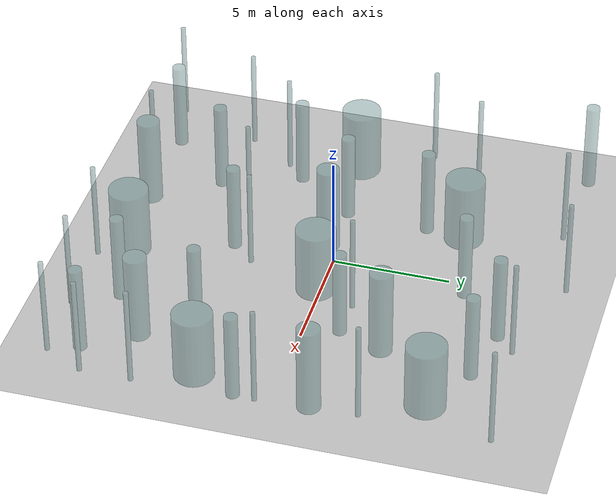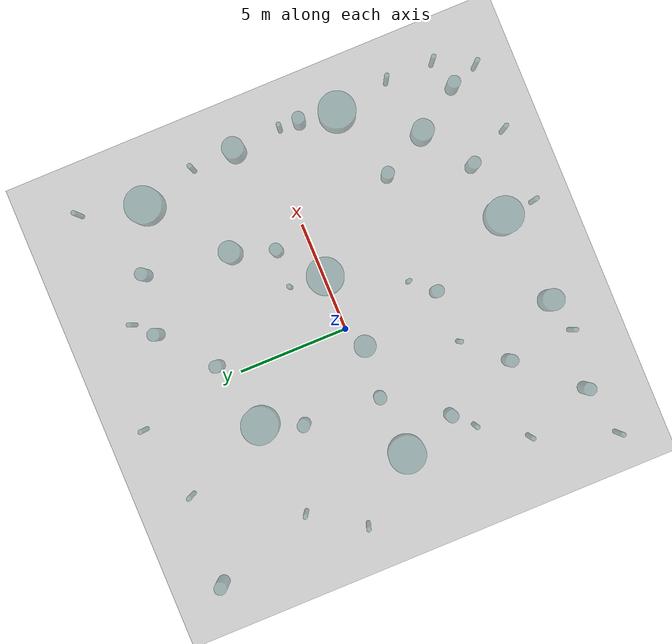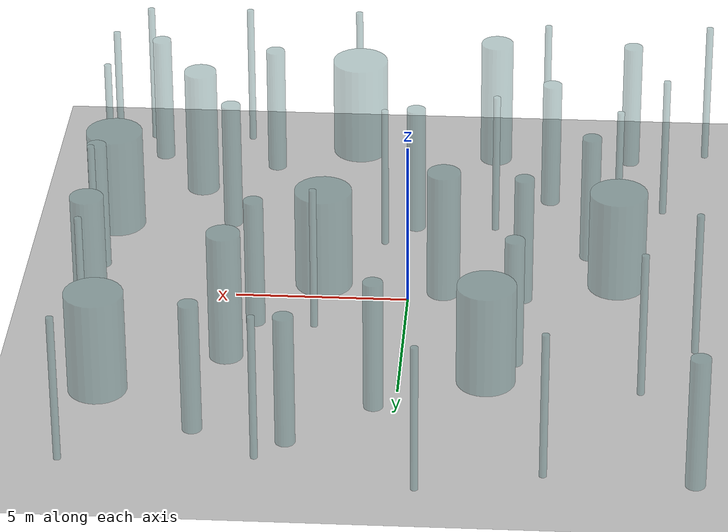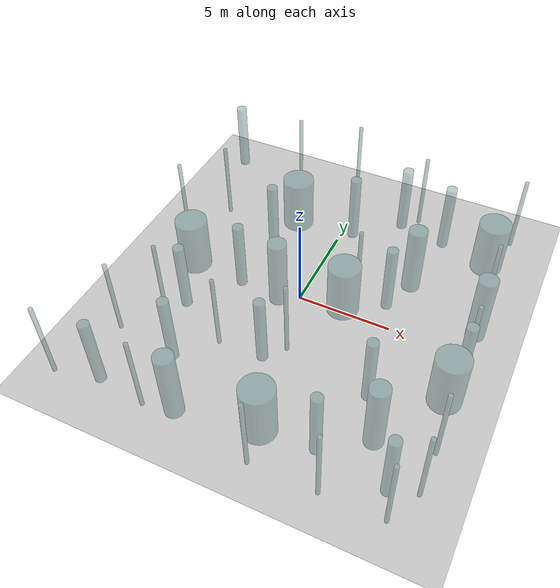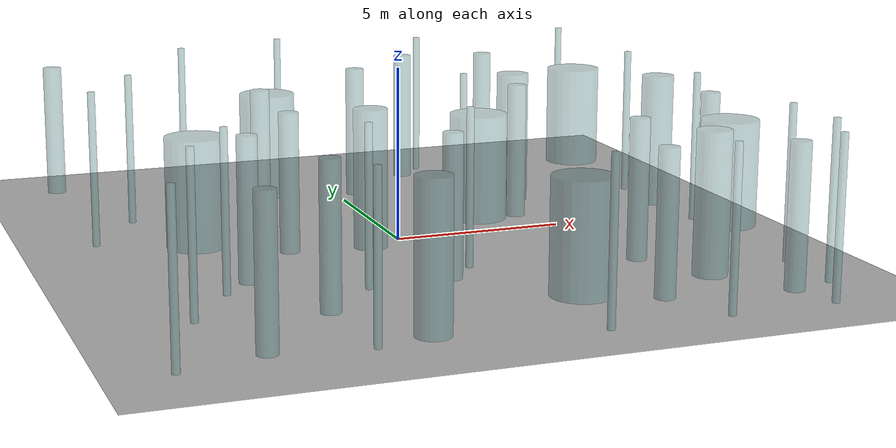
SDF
<sdf version="1.6">
 <world name="default">
  <light name="sun" type="directional">
   <pose>0 0 10 0 -0 0</pose>
   <diffuse>0.8 0.8 0.8 1</diffuse>
   <specular>0.2 0.2 0.2 1</specular>
   <attenuation>
    <range>1000</range>
    <constant>0.9</constant>
    <linear>0.01</linear>
    <quadratic>0.001</quadratic>
   </attenuation>
   <direction>-0.5 0.1 -0.9</direction>
  </light>
  <model name="ground_plane">
   <static>1</static>
   <link name="link">
    <collision name="collision">
     <geometry><plane><normal>0 0 1</normal><size>100 100</size></plane></geometry>
     <surface><friction><ode><mu>100</mu><mu2>50</mu2></ode></friction></surface>
    </collision>
    <visual name="visual">
     <cast_shadows>0</cast_shadows>
     <geometry><plane><normal>0 0 1</normal><size>100 100</size></plane></geometry>
     <material>
      <script><uri>file://media/materials/scripts/gazebo.material</uri><name>Gazebo/Grey</name></script>
     </material>
    </visual>
   </link>
  </model>
  <gravity>0 0 -9.8</gravity>
  <magnetic_field>6e-06 2.3e-05 -4.2e-05</magnetic_field>
  <atmosphere type="adiabatic"/>
  <physics name="default_physics" default="0" type="ode">
   <max_step_size>0.001</max_step_size>
   <real_time_factor>1</real_time_factor>
   <real_time_update_rate>1000</real_time_update_rate>
  </physics>
  <scene><ambient>0.2 0.2 0.2 1</ambient><background>0.7 0.7 0.7 1</background><shadows>0</shadows></scene>
  <audio><device>default</device></audio>
  <spherical_coordinates>
   <surface_model>EARTH_WGS84</surface_model>
   <latitude_deg>0</latitude_deg>
   <longitude_deg>0</longitude_deg>
   <elevation>0</elevation>
   <heading_deg>0</heading_deg>
  </spherical_coordinates>
  <model name="cylinders">
   <link name="link_clone">
    <inertial>
     <mass>1</mass>
     <inertia><ixx>0.145833</ixx><ixy>0</ixy><ixz>0</ixz><iyy>0.145833</iyy><iyz>0</iyz><izz>0.125</izz></inertia>
    </inertial>
    <pose>-2.72794 0.553847 -0 -0 -0 -0.001272</pose>
    <visual name="visual">
     <geometry><cylinder><radius>0.280725</radius><length>4</length></cylinder></geometry>
     <material>
      <script><name>Gazebo/Grey</name><uri>file://media/materials/scripts/gazebo.material</uri></script>
      <ambient>0.1 0.1 0.9 0.6</ambient>
      <shader type="vertex"><normal_map>__default__</normal_map></shader>
      <diffuse>0.3 0.5 0.5 0.4</diffuse>
      <specular>0.01 0.01 0.01 1</specular>
      <emissive>0 0 0 1</emissive>
      <lighting>1</lighting>
     </material>
    </visual>
    <collision name="collision">
     <geometry><cylinder><radius>0.280725</radius><length>4</length></cylinder></geometry>
     <surface>
      <friction>
       <ode><mu>1</mu><mu2>1</mu2><fdir1>0 0 0</fdir1><slip1>0</slip1><slip2>0</slip2></ode>
       <torsional>
        <coefficient>1</coefficient>
        <patch_radius>0</patch_radius>
        <surface_radius>0</surface_radius>
        <use_patch_radius>1</use_patch_radius>
        <ode><slip>0</slip></ode>
       </torsional>
      </friction>
      <bounce><restitution_coefficient>0</restitution_coefficient><threshold>1e+06</threshold></bounce>
      <contact>
       <collide_without_contact>0</collide_without_contact>
       <collide_without_contact_bitmask>1</collide_without_contact_bitmask>
       <collide_bitmask>1</collide_bitmask>
       <ode>
        <soft_cfm>0</soft_cfm>
        <soft_erp>0.2</soft_erp>
        <kp>1e+13</kp>
        <kd>1</kd>
        <max_vel>0.01</max_vel>
        <min_depth>0</min_depth>
       </ode>
       <bullet>
        <split_impulse>1</split_impulse>
        <split_impulse_penetration_threshold>-0.01</split_impulse_penetration_threshold>
        <soft_cfm>0</soft_cfm>
        <soft_erp>0.2</soft_erp>
        <kp>1e+13</kp>
        <kd>1</kd>
       </bullet>
      </contact>
     </surface>
    </collision>
   </link>
   <link name="link_clone_0">
    <inertial>
     <mass>1</mass>
     <inertia><ixx>0.145833</ixx><ixy>0</ixy><ixz>0</ixz><iyy>0.145833</iyy><iyz>0</iyz><izz>0.125</izz></inertia>
    </inertial>
    <pose>-2.56006 4.06753 -1e-06 -0 -0 -0.001272</pose>
    <visual name="visual">
     <geometry><cylinder><radius>0.280725</radius><length>4</length></cylinder></geometry>
     <material>
      <script><name>Gazebo/Grey</name><uri>file://media/materials/scripts/gazebo.material</uri></script>
      <ambient>0.1 0.1 0.9 0.6</ambient>
      <shader type="vertex"><normal_map>__default__</normal_map></shader>
      <diffuse>0.3 0.5 0.5 0.4</diffuse>
      <specular>0.01 0.01 0.01 1</specular>
      <emissive>0 0 0 1</emissive>
      <lighting>1</lighting>
     </material>
    </visual>
    <collision name="collision">
     <geometry><cylinder><radius>0.280725</radius><length>4</length></cylinder></geometry>
     <surface>
      <friction>
       <ode><mu>1</mu><mu2>1</mu2><fdir1>0 0 0</fdir1><slip1>0</slip1><slip2>0</slip2></ode>
       <torsional>
        <coefficient>1</coefficient>
        <patch_radius>0</patch_radius>
        <surface_radius>0</surface_radius>
        <use_patch_radius>1</use_patch_radius>
        <ode><slip>0</slip></ode>
       </torsional>
      </friction>
      <bounce><restitution_coefficient>0</restitution_coefficient><threshold>1e+06</threshold></bounce>
      <contact>
       <collide_without_contact>0</collide_without_contact>
       <collide_without_contact_bitmask>1</collide_without_contact_bitmask>
       <collide_bitmask>1</collide_bitmask>
       <ode>
        <soft_cfm>0</soft_cfm>
        <soft_erp>0.2</soft_erp>
        <kp>1e+13</kp>
        <kd>1</kd>
        <max_vel>0.01</max_vel>
        <min_depth>0</min_depth>
       </ode>
       <bullet>
        <split_impulse>1</split_impulse>
        <split_impulse_penetration_threshold>-0.01</split_impulse_penetration_threshold>
        <soft_cfm>0</soft_cfm>
        <soft_erp>0.2</soft_erp>
        <kp>1e+13</kp>
        <kd>1</kd>
       </bullet>
      </contact>
     </surface>
    </collision>
   </link>
   <link name="link_clone_1">
    <inertial>
     <mass>1</mass>
     <inertia><ixx>0.145833</ixx><ixy>0</ixy><ixz>0</ixz><iyy>0.145833</iyy><iyz>0</iyz><izz>0.125</izz></inertia>
    </inertial>
    <pose>1.23896 6.59521 -0 -0 -0 -0.001272</pose>
    <visual name="visual">
     <geometry><cylinder><radius>0.280725</radius><length>4</length></cylinder></geometry>
     <material>
      <script><name>Gazebo/Grey</name><uri>file://media/materials/scripts/gazebo.material</uri></script>
      <ambient>0.1 0.1 0.9 0.6</ambient>
      <shader type="vertex"><normal_map>__default__</normal_map></shader>
      <diffuse>0.3 0.5 0.5 0.4</diffuse>
      <specular>0.01 0.01 0.01 1</specular>
      <emissive>0 0 0 1</emissive>
      <lighting>1</lighting>
     </material>
    </visual>
    <collision name="collision">
     <geometry><cylinder><radius>0.280725</radius><length>4</length></cylinder></geometry>
     <surface>
      <friction>
       <ode><mu>1</mu><mu2>1</mu2><fdir1>0 0 0</fdir1><slip1>0</slip1><slip2>0</slip2></ode>
       <torsional>
        <coefficient>1</coefficient>
        <patch_radius>0</patch_radius>
        <surface_radius>0</surface_radius>
        <use_patch_radius>1</use_patch_radius>
        <ode><slip>0</slip></ode>
       </torsional>
      </friction>
      <bounce><restitution_coefficient>0</restitution_coefficient><threshold>1e+06</threshold></bounce>
      <contact>
       <collide_without_contact>0</collide_without_contact>
       <collide_without_contact_bitmask>1</collide_without_contact_bitmask>
       <collide_bitmask>1</collide_bitmask>
       <ode>
        <soft_cfm>0</soft_cfm>
        <soft_erp>0.2</soft_erp>
        <kp>1e+13</kp>
        <kd>1</kd>
        <max_vel>0.01</max_vel>
        <min_depth>0</min_depth>
       </ode>
       <bullet>
        <split_impulse>1</split_impulse>
        <split_impulse_penetration_threshold>-0.01</split_impulse_penetration_threshold>
        <soft_cfm>0</soft_cfm>
        <soft_erp>0.2</soft_erp>
        <kp>1e+13</kp>
        <kd>1</kd>
       </bullet>
      </contact>
     </surface>
    </collision>
   </link>
   <link name="link_clone_10">
    <inertial>
     <mass>1</mass>
     <inertia><ixx>0.145833</ixx><ixy>0</ixy><ixz>0</ixz><iyy>0.145833</iyy><iyz>0</iyz><izz>0.125</izz></inertia>
    </inertial>
    <pose>6.10285 -3.45416 1e-06 -0 -0 -0.001272</pose>
    <visual name="visual">
     <geometry><cylinder><radius>0.280725</radius><length>4</length></cylinder></geometry>
     <material>
      <script><name>Gazebo/Grey</name><uri>file://media/materials/scripts/gazebo.material</uri></script>
      <ambient>0.1 0.1 0.9 0.6</ambient>
      <shader type="vertex"><normal_map>__default__</normal_map></shader>
      <diffuse>0.3 0.5 0.5 0.4</diffuse>
      <specular>0.01 0.01 0.01 1</specular>
      <emissive>0 0 0 1</emissive>
      <lighting>1</lighting>
     </material>
    </visual>
    <collision name="collision">
     <geometry><cylinder><radius>0.280725</radius><length>4</length></cylinder></geometry>
     <surface>
      <friction>
       <ode><mu>1</mu><mu2>1</mu2><fdir1>0 0 0</fdir1><slip1>0</slip1><slip2>0</slip2></ode>
       <torsional>
        <coefficient>1</coefficient>
        <patch_radius>0</patch_radius>
        <surface_radius>0</surface_radius>
        <use_patch_radius>1</use_patch_radius>
        <ode><slip>0</slip></ode>
       </torsional>
      </friction>
      <bounce><restitution_coefficient>0</restitution_coefficient><threshold>1e+06</threshold></bounce>
      <contact>
       <collide_without_contact>0</collide_without_contact>
       <collide_without_contact_bitmask>1</collide_without_contact_bitmask>
       <collide_bitmask>1</collide_bitmask>
       <ode>
        <soft_cfm>0</soft_cfm>
        <soft_erp>0.2</soft_erp>
        <kp>1e+13</kp>
        <kd>1</kd>
        <max_vel>0.01</max_vel>
        <min_depth>0</min_depth>
       </ode>
       <bullet>
        <split_impulse>1</split_impulse>
        <split_impulse_penetration_threshold>-0.01</split_impulse_penetration_threshold>
        <soft_cfm>0</soft_cfm>
        <soft_erp>0.2</soft_erp>
        <kp>1e+13</kp>
        <kd>1</kd>
       </bullet>
      </contact>
     </surface>
    </collision>
   </link>
   <link name="link_clone_11">
    <inertial>
     <mass>1</mass>
     <inertia><ixx>0.145833</ixx><ixy>0</ixy><ixz>0</ixz><iyy>0.145833</iyy><iyz>0</iyz><izz>0.125</izz></inertia>
    </inertial>
    <pose>8.62363 -7.57073 2e-06 -0 -0 -0.001272</pose>
    <visual name="visual">
     <geometry><cylinder><radius>0.280725</radius><length>4</length></cylinder></geometry>
     <material>
      <script><name>Gazebo/Grey</name><uri>file://media/materials/scripts/gazebo.material</uri></script>
      <ambient>0.1 0.1 0.9 0.6</ambient>
      <shader type="vertex"><normal_map>__default__</normal_map></shader>
      <diffuse>0.3 0.5 0.5 0.4</diffuse>
      <specular>0.01 0.01 0.01 1</specular>
      <emissive>0 0 0 1</emissive>
      <lighting>1</lighting>
     </material>
    </visual>
    <collision name="collision">
     <geometry><cylinder><radius>0.280725</radius><length>4</length></cylinder></geometry>
     <surface>
      <friction>
       <ode><mu>1</mu><mu2>1</mu2><fdir1>0 0 0</fdir1><slip1>0</slip1><slip2>0</slip2></ode>
       <torsional>
        <coefficient>1</coefficient>
        <patch_radius>0</patch_radius>
        <surface_radius>0</surface_radius>
        <use_patch_radius>1</use_patch_radius>
        <ode><slip>0</slip></ode>
       </torsional>
      </friction>
      <bounce><restitution_coefficient>0</restitution_coefficient><threshold>1e+06</threshold></bounce>
      <contact>
       <collide_without_contact>0</collide_without_contact>
       <collide_without_contact_bitmask>1</collide_without_contact_bitmask>
       <collide_bitmask>1</collide_bitmask>
       <ode>
        <soft_cfm>0</soft_cfm>
        <soft_erp>0.2</soft_erp>
        <kp>1e+13</kp>
        <kd>1</kd>
        <max_vel>0.01</max_vel>
        <min_depth>0</min_depth>
       </ode>
       <bullet>
        <split_impulse>1</split_impulse>
        <split_impulse_penetration_threshold>-0.01</split_impulse_penetration_threshold>
        <soft_cfm>0</soft_cfm>
        <soft_erp>0.2</soft_erp>
        <kp>1e+13</kp>
        <kd>1</kd>
       </bullet>
      </contact>
     </surface>
    </collision>
   </link>
   <link name="link_clone_11_clone">
    <inertial>
     <mass>1</mass>
     <inertia><ixx>0.145833</ixx><ixy>0</ixy><ixz>0</ixz><iyy>0.145833</iyy><iyz>0</iyz><izz>0.125</izz></inertia>
    </inertial>
    <pose>-5.81358 -7.92747 1e-06 -0 -0 -0.002544</pose>
    <visual name="visual">
     <geometry><cylinder><radius>0.280725</radius><length>4</length></cylinder></geometry>
     <material>
      <script><name>Gazebo/Grey</name><uri>file://media/materials/scripts/gazebo.material</uri></script>
      <ambient>0.1 0.1 0.9 0.6</ambient>
      <shader type="vertex"><normal_map>__default__</normal_map></shader>
      <diffuse>0.3 0.5 0.5 0.4</diffuse>
      <specular>0.01 0.01 0.01 1</specular>
      <emissive>0 0 0 1</emissive>
      <lighting>1</lighting>
     </material>
    </visual>
    <collision name="collision">
     <geometry><cylinder><radius>0.280725</radius><length>4</length></cylinder></geometry>
     <surface>
      <friction>
       <ode><mu>1</mu><mu2>1</mu2><fdir1>0 0 0</fdir1><slip1>0</slip1><slip2>0</slip2></ode>
       <torsional>
        <coefficient>1</coefficient>
        <patch_radius>0</patch_radius>
        <surface_radius>0</surface_radius>
        <use_patch_radius>1</use_patch_radius>
        <ode><slip>0</slip></ode>
       </torsional>
      </friction>
      <bounce><restitution_coefficient>0</restitution_coefficient><threshold>1e+06</threshold></bounce>
      <contact>
       <collide_without_contact>0</collide_without_contact>
       <collide_without_contact_bitmask>1</collide_without_contact_bitmask>
       <collide_bitmask>1</collide_bitmask>
       <ode>
        <soft_cfm>0</soft_cfm>
        <soft_erp>0.2</soft_erp>
        <kp>1e+13</kp>
        <kd>1</kd>
        <max_vel>0.01</max_vel>
        <min_depth>0</min_depth>
       </ode>
       <bullet>
        <split_impulse>1</split_impulse>
        <split_impulse_penetration_threshold>-0.01</split_impulse_penetration_threshold>
        <soft_cfm>0</soft_cfm>
        <soft_erp>0.2</soft_erp>
        <kp>1e+13</kp>
        <kd>1</kd>
       </bullet>
      </contact>
     </surface>
    </collision>
   </link>
   <link name="link_clone_11_clone_0">
    <inertial>
     <mass>2.96402</mass>
     <inertia><ixx>4.12512</ixx><ixy>0</ixy><ixz>0</ixz><iyy>4.12512</iyy><iyz>0</iyz><izz>0.346176</izz></inertia>
    </inertial>
    <pose>-1.65639 -7.9506 2e-06 -0 -0 -0.002544</pose>
    <visual name="visual">
     <geometry><cylinder><radius>0.483307</radius><length>4</length></cylinder></geometry>
     <material>
      <script><name>Gazebo/Grey</name><uri>file://media/materials/scripts/gazebo.material</uri></script>
      <ambient>0.1 0.1 0.9 0.6</ambient>
      <shader type="vertex"><normal_map>__default__</normal_map></shader>
      <diffuse>0.3 0.5 0.5 0.4</diffuse>
      <specular>0.01 0.01 0.01 1</specular>
      <emissive>0 0 0 1</emissive>
      <lighting>1</lighting>
     </material>
    </visual>
    <collision name="collision">
     <geometry><cylinder><radius>0.483307</radius><length>4</length></cylinder></geometry>
     <surface>
      <friction>
       <ode><mu>1</mu><mu2>1</mu2><fdir1>0 0 0</fdir1><slip1>0</slip1><slip2>0</slip2></ode>
       <torsional>
        <coefficient>1</coefficient>
        <patch_radius>0</patch_radius>
        <surface_radius>0</surface_radius>
        <use_patch_radius>1</use_patch_radius>
        <ode><slip>0</slip></ode>
       </torsional>
      </friction>
      <bounce><restitution_coefficient>0</restitution_coefficient><threshold>1e+06</threshold></bounce>
      <contact>
       <collide_without_contact>0</collide_without_contact>
       <collide_without_contact_bitmask>1</collide_without_contact_bitmask>
       <collide_bitmask>1</collide_bitmask>
       <ode>
        <soft_cfm>0</soft_cfm>
        <soft_erp>0.2</soft_erp>
        <kp>1e+13</kp>
        <kd>1</kd>
        <max_vel>0.01</max_vel>
        <min_depth>0</min_depth>
       </ode>
       <bullet>
        <split_impulse>1</split_impulse>
        <split_impulse_penetration_threshold>-0.01</split_impulse_penetration_threshold>
        <soft_cfm>0</soft_cfm>
        <soft_erp>0.2</soft_erp>
        <kp>1e+13</kp>
        <kd>1</kd>
       </bullet>
      </contact>
     </surface>
    </collision>
   </link>
   <link name="link_clone_11_clone_0_clone">
    <inertial>
     <mass>2.96402</mass>
     <inertia><ixx>4.12512</ixx><ixy>0</ixy><ixz>0</ixz><iyy>4.12512</iyy><iyz>0</iyz><izz>0.346176</izz></inertia>
    </inertial>
    <pose>-0.406852 0.309702 2e-06 -0 -0 -0.003816</pose>
    <visual name="visual">
     <geometry><cylinder><radius>0.483307</radius><length>4</length></cylinder></geometry>
     <material>
      <script><name>Gazebo/Grey</name><uri>file://media/materials/scripts/gazebo.material</uri></script>
      <ambient>0.1 0.1 0.9 0.6</ambient>
      <shader type="vertex"><normal_map>__default__</normal_map></shader>
      <diffuse>0.3 0.5 0.5 0.4</diffuse>
      <specular>0.01 0.01 0.01 1</specular>
      <emissive>0 0 0 1</emissive>
      <lighting>1</lighting>
     </material>
    </visual>
    <collision name="collision">
     <geometry><cylinder><radius>0.483307</radius><length>4</length></cylinder></geometry>
     <surface>
      <friction>
       <ode><mu>1</mu><mu2>1</mu2><fdir1>0 0 0</fdir1><slip1>0</slip1><slip2>0</slip2></ode>
       <torsional>
        <coefficient>1</coefficient>
        <patch_radius>0</patch_radius>
        <surface_radius>0</surface_radius>
        <use_patch_radius>1</use_patch_radius>
        <ode><slip>0</slip></ode>
       </torsional>
      </friction>
      <bounce><restitution_coefficient>0</restitution_coefficient><threshold>1e+06</threshold></bounce>
      <contact>
       <collide_without_contact>0</collide_without_contact>
       <collide_without_contact_bitmask>1</collide_without_contact_bitmask>
       <collide_bitmask>1</collide_bitmask>
       <ode>
        <soft_cfm>0</soft_cfm>
        <soft_erp>0.2</soft_erp>
        <kp>1e+13</kp>
        <kd>1</kd>
        <max_vel>0.01</max_vel>
        <min_depth>0</min_depth>
       </ode>
       <bullet>
        <split_impulse>1</split_impulse>
        <split_impulse_penetration_threshold>-0.01</split_impulse_penetration_threshold>
        <soft_cfm>0</soft_cfm>
        <soft_erp>0.2</soft_erp>
        <kp>1e+13</kp>
        <kd>1</kd>
       </bullet>
      </contact>
     </surface>
    </collision>
   </link>
   <link name="link_clone_11_clone_0_clone_0">
    <inertial>
     <mass>2.96402</mass>
     <inertia><ixx>4.12512</ixx><ixy>0</ixy><ixz>0</ixz><iyy>4.12512</iyy><iyz>0</iyz><izz>0.346176</izz></inertia>
    </inertial>
    <pose>5.5796 4.15801 3e-06 -0 -0 -0.003816</pose>
    <visual name="visual">
     <geometry><cylinder><radius>0.483307</radius><length>4</length></cylinder></geometry>
     <material>
      <script><name>Gazebo/Grey</name><uri>file://media/materials/scripts/gazebo.material</uri></script>
      <ambient>0.1 0.1 0.9 0.6</ambient>
      <shader type="vertex"><normal_map>__default__</normal_map></shader>
      <diffuse>0.3 0.5 0.5 0.4</diffuse>
      <specular>0.01 0.01 0.01 1</specular>
      <emissive>0 0 0 1</emissive>
      <lighting>1</lighting>
     </material>
    </visual>
    <collision name="collision">
     <geometry><cylinder><radius>0.483307</radius><length>4</length></cylinder></geometry>
     <surface>
      <friction>
       <ode><mu>1</mu><mu2>1</mu2><fdir1>0 0 0</fdir1><slip1>0</slip1><slip2>0</slip2></ode>
       <torsional>
        <coefficient>1</coefficient>
        <patch_radius>0</patch_radius>
        <surface_radius>0</surface_radius>
        <use_patch_radius>1</use_patch_radius>
        <ode><slip>0</slip></ode>
       </torsional>
      </friction>
      <bounce><restitution_coefficient>0</restitution_coefficient><threshold>1e+06</threshold></bounce>
      <contact>
       <collide_without_contact>0</collide_without_contact>
       <collide_without_contact_bitmask>1</collide_without_contact_bitmask>
       <collide_bitmask>1</collide_bitmask>
       <ode>
        <soft_cfm>0</soft_cfm>
        <soft_erp>0.2</soft_erp>
        <kp>1e+13</kp>
        <kd>1</kd>
        <max_vel>0.01</max_vel>
        <min_depth>0</min_depth>
       </ode>
       <bullet>
        <split_impulse>1</split_impulse>
        <split_impulse_penetration_threshold>-0.01</split_impulse_penetration_threshold>
        <soft_cfm>0</soft_cfm>
        <soft_erp>0.2</soft_erp>
        <kp>1e+13</kp>
        <kd>1</kd>
       </bullet>
      </contact>
     </surface>
    </collision>
   </link>
   <link name="link_clone_11_clone_0_clone_1">
    <inertial>
     <mass>2.96402</mass>
     <inertia><ixx>4.12512</ixx><ixy>0</ixy><ixz>0</ixz><iyy>4.12512</iyy><iyz>0</iyz><izz>0.346176</izz></inertia>
    </inertial>
    <pose>9.65056 2.30999 3e-06 -0 -0 -0.003816</pose>
    <visual name="visual">
     <geometry><cylinder><radius>0.483307</radius><length>4</length></cylinder></geometry>
     <material>
      <script><name>Gazebo/Grey</name><uri>file://media/materials/scripts/gazebo.material</uri></script>
      <ambient>0.1 0.1 0.9 0.6</ambient>
      <shader type="vertex"><normal_map>__default__</normal_map></shader>
      <diffuse>0.3 0.5 0.5 0.4</diffuse>
      <specular>0.01 0.01 0.01 1</specular>
      <emissive>0 0 0 1</emissive>
      <lighting>1</lighting>
     </material>
    </visual>
    <collision name="collision">
     <geometry><cylinder><radius>0.483307</radius><length>4</length></cylinder></geometry>
     <surface>
      <friction>
       <ode><mu>1</mu><mu2>1</mu2><fdir1>0 0 0</fdir1><slip1>0</slip1><slip2>0</slip2></ode>
       <torsional>
        <coefficient>1</coefficient>
        <patch_radius>0</patch_radius>
        <surface_radius>0</surface_radius>
        <use_patch_radius>1</use_patch_radius>
        <ode><slip>0</slip></ode>
       </torsional>
      </friction>
      <bounce><restitution_coefficient>0</restitution_coefficient><threshold>1e+06</threshold></bounce>
      <contact>
       <collide_without_contact>0</collide_without_contact>
       <collide_without_contact_bitmask>1</collide_without_contact_bitmask>
       <collide_bitmask>1</collide_bitmask>
       <ode>
        <soft_cfm>0</soft_cfm>
        <soft_erp>0.2</soft_erp>
        <kp>1e+13</kp>
        <kd>1</kd>
        <max_vel>0.01</max_vel>
        <min_depth>0</min_depth>
       </ode>
       <bullet>
        <split_impulse>1</split_impulse>
        <split_impulse_penetration_threshold>-0.01</split_impulse_penetration_threshold>
        <soft_cfm>0</soft_cfm>
        <soft_erp>0.2</soft_erp>
        <kp>1e+13</kp>
        <kd>1</kd>
       </bullet>
      </contact>
     </surface>
    </collision>
   </link>
   <link name="link_clone_11_clone_0_clone_2">
    <inertial>
     <mass>2.96402</mass>
     <inertia><ixx>4.12512</ixx><ixy>0</ixy><ixz>0</ixz><iyy>4.12512</iyy><iyz>0</iyz><izz>0.346176</izz></inertia>
    </inertial>
    <pose>7.2329 -5.55542 3e-06 -0 -0 -0.003816</pose>
    <visual name="visual">
     <geometry><cylinder><radius>0.483307</radius><length>4</length></cylinder></geometry>
     <material>
      <script><name>Gazebo/Grey</name><uri>file://media/materials/scripts/gazebo.material</uri></script>
      <ambient>0.1 0.1 0.9 0.6</ambient>
      <shader type="vertex"><normal_map>__default__</normal_map></shader>
      <diffuse>0.3 0.5 0.5 0.4</diffuse>
      <specular>0.01 0.01 0.01 1</specular>
      <emissive>0 0 0 1</emissive>
      <lighting>1</lighting>
     </material>
    </visual>
    <collision name="collision">
     <geometry><cylinder><radius>0.483307</radius><length>4</length></cylinder></geometry>
     <surface>
      <friction>
       <ode><mu>1</mu><mu2>1</mu2><fdir1>0 0 0</fdir1><slip1>0</slip1><slip2>0</slip2></ode>
       <torsional>
        <coefficient>1</coefficient>
        <patch_radius>0</patch_radius>
        <surface_radius>0</surface_radius>
        <use_patch_radius>1</use_patch_radius>
        <ode><slip>0</slip></ode>
       </torsional>
      </friction>
      <bounce><restitution_coefficient>0</restitution_coefficient><threshold>1e+06</threshold></bounce>
      <contact>
       <collide_without_contact>0</collide_without_contact>
       <collide_without_contact_bitmask>1</collide_without_contact_bitmask>
       <collide_bitmask>1</collide_bitmask>
       <ode>
        <soft_cfm>0</soft_cfm>
        <soft_erp>0.2</soft_erp>
        <kp>1e+13</kp>
        <kd>1</kd>
        <max_vel>0.01</max_vel>
        <min_depth>0</min_depth>
       </ode>
       <bullet>
        <split_impulse>1</split_impulse>
        <split_impulse_penetration_threshold>-0.01</split_impulse_penetration_threshold>
        <soft_cfm>0</soft_cfm>
        <soft_erp>0.2</soft_erp>
        <kp>1e+13</kp>
        <kd>1</kd>
       </bullet>
      </contact>
     </surface>
    </collision>
   </link>
   <link name="link_clone_11_clone_1">
    <inertial>
     <mass>1</mass>
     <inertia><ixx>0.145833</ixx><ixy>0</ixy><ixz>0</ixz><iyy>0.145833</iyy><iyz>0</iyz><izz>0.125</izz></inertia>
    </inertial>
    <pose>5.08484 -7.05522 3e-06 -0 -0 -0.002544</pose>
    <visual name="visual">
     <geometry><cylinder><radius>0.280725</radius><length>4</length></cylinder></geometry>
     <material>
      <script><name>Gazebo/Grey</name><uri>file://media/materials/scripts/gazebo.material</uri></script>
      <ambient>0.1 0.1 0.9 0.6</ambient>
      <shader type="vertex"><normal_map>__default__</normal_map></shader>
      <diffuse>0.3 0.5 0.5 0.4</diffuse>
      <specular>0.01 0.01 0.01 1</specular>
      <emissive>0 0 0 1</emissive>
      <lighting>1</lighting>
     </material>
    </visual>
    <collision name="collision">
     <geometry><cylinder><radius>0.280725</radius><length>4</length></cylinder></geometry>
     <surface>
      <friction>
       <ode><mu>1</mu><mu2>1</mu2><fdir1>0 0 0</fdir1><slip1>0</slip1><slip2>0</slip2></ode>
       <torsional>
        <coefficient>1</coefficient>
        <patch_radius>0</patch_radius>
        <surface_radius>0</surface_radius>
        <use_patch_radius>1</use_patch_radius>
        <ode><slip>0</slip></ode>
       </torsional>
      </friction>
      <bounce><restitution_coefficient>0</restitution_coefficient><threshold>1e+06</threshold></bounce>
      <contact>
       <collide_without_contact>0</collide_without_contact>
       <collide_without_contact_bitmask>1</collide_without_contact_bitmask>
       <collide_bitmask>1</collide_bitmask>
       <ode>
        <soft_cfm>0</soft_cfm>
        <soft_erp>0.2</soft_erp>
        <kp>1e+13</kp>
        <kd>1</kd>
        <max_vel>0.01</max_vel>
        <min_depth>0</min_depth>
       </ode>
       <bullet>
        <split_impulse>1</split_impulse>
        <split_impulse_penetration_threshold>-0.01</split_impulse_penetration_threshold>
        <soft_cfm>0</soft_cfm>
        <soft_erp>0.2</soft_erp>
        <kp>1e+13</kp>
        <kd>1</kd>
       </bullet>
      </contact>
     </surface>
    </collision>
   </link>
   <link name="link_clone_11_clone_1_clone">
    <inertial>
     <mass>0.168862</mass>
     <inertia>
      <ixx>0.33323</ixx>
      <ixy>0</ixy>
      <ixz>0</ixz>
      <iyy>0.33323</iyy>
      <iyz>0</iyz>
      <izz>0.000924096</izz>
     </inertia>
    </inertial>
    <pose>9.79655 0.113416 5e-06 -0 -0 -0.003816</pose>
    <visual name="visual">
     <geometry><cylinder><radius>0.104618</radius><length>4.8629</length></cylinder></geometry>
     <material>
      <script><name>Gazebo/Grey</name><uri>file://media/materials/scripts/gazebo.material</uri></script>
      <ambient>0.1 0.1 0.9 0.6</ambient>
      <shader type="vertex"><normal_map>__default__</normal_map></shader>
      <diffuse>0.3 0.5 0.5 0.4</diffuse>
      <specular>0.01 0.01 0.01 1</specular>
      <emissive>0 0 0 1</emissive>
      <lighting>1</lighting>
     </material>
    </visual>
    <collision name="collision">
     <geometry><cylinder><radius>0.104618</radius><length>4.8629</length></cylinder></geometry>
     <surface>
      <friction>
       <ode><mu>1</mu><mu2>1</mu2><fdir1>0 0 0</fdir1><slip1>0</slip1><slip2>0</slip2></ode>
       <torsional>
        <coefficient>1</coefficient>
        <patch_radius>0</patch_radius>
        <surface_radius>0</surface_radius>
        <use_patch_radius>1</use_patch_radius>
        <ode><slip>0</slip></ode>
       </torsional>
      </friction>
      <bounce><restitution_coefficient>0</restitution_coefficient><threshold>1e+06</threshold></bounce>
      <contact>
       <collide_without_contact>0</collide_without_contact>
       <collide_without_contact_bitmask>1</collide_without_contact_bitmask>
       <collide_bitmask>1</collide_bitmask>
       <ode>
        <soft_cfm>0</soft_cfm>
        <soft_erp>0.2</soft_erp>
        <kp>1e+13</kp>
        <kd>1</kd>
        <max_vel>0.01</max_vel>
        <min_depth>0</min_depth>
       </ode>
       <bullet>
        <split_impulse>1</split_impulse>
        <split_impulse_penetration_threshold>-0.01</split_impulse_penetration_threshold>
        <soft_cfm>0</soft_cfm>
        <soft_erp>0.2</soft_erp>
        <kp>1e+13</kp>
        <kd>1</kd>
       </bullet>
      </contact>
     </surface>
    </collision>
   </link>
   <link name="link_clone_11_clone_1_clone_0">
    <inertial>
     <mass>0.168862</mass>
     <inertia>
      <ixx>0.33323</ixx>
      <ixy>0</ixy>
      <ixz>0</ixz>
      <iyy>0.33323</iyy>
      <iyz>0</iyz>
      <izz>0.000924096</izz>
     </inertia>
    </inertial>
    <pose>9.95161 -4.98191 5e-06 -0 -0 -0.003816</pose>
    <visual name="visual">
     <geometry><cylinder><radius>0.104618</radius><length>4.8629</length></cylinder></geometry>
     <material>
      <script><name>Gazebo/Grey</name><uri>file://media/materials/scripts/gazebo.material</uri></script>
      <ambient>0.1 0.1 0.9 0.6</ambient>
      <shader type="vertex"><normal_map>__default__</normal_map></shader>
      <diffuse>0.3 0.5 0.5 0.4</diffuse>
      <specular>0.01 0.01 0.01 1</specular>
      <emissive>0 0 0 1</emissive>
      <lighting>1</lighting>
     </material>
    </visual>
    <collision name="collision">
     <geometry><cylinder><radius>0.104618</radius><length>4.8629</length></cylinder></geometry>
     <surface>
      <friction>
       <ode><mu>1</mu><mu2>1</mu2><fdir1>0 0 0</fdir1><slip1>0</slip1><slip2>0</slip2></ode>
       <torsional>
        <coefficient>1</coefficient>
        <patch_radius>0</patch_radius>
        <surface_radius>0</surface_radius>
        <use_patch_radius>1</use_patch_radius>
        <ode><slip>0</slip></ode>
       </torsional>
      </friction>
      <bounce><restitution_coefficient>0</restitution_coefficient><threshold>1e+06</threshold></bounce>
      <contact>
       <collide_without_contact>0</collide_without_contact>
       <collide_without_contact_bitmask>1</collide_without_contact_bitmask>
       <collide_bitmask>1</collide_bitmask>
       <ode>
        <soft_cfm>0</soft_cfm>
        <soft_erp>0.2</soft_erp>
        <kp>1e+13</kp>
        <kd>1</kd>
        <max_vel>0.01</max_vel>
        <min_depth>0</min_depth>
       </ode>
       <bullet>
        <split_impulse>1</split_impulse>
        <split_impulse_penetration_threshold>-0.01</split_impulse_penetration_threshold>
        <soft_cfm>0</soft_cfm>
        <soft_erp>0.2</soft_erp>
        <kp>1e+13</kp>
        <kd>1</kd>
       </bullet>
      </contact>
     </surface>
    </collision>
   </link>
   <link name="link_clone_11_clone_1_clone_1">
    <inertial>
     <mass>0.168862</mass>
     <inertia>
      <ixx>0.33323</ixx>
      <ixy>0</ixy>
      <ixz>0</ixz>
      <iyy>0.33323</iyy>
      <iyz>0</iyz>
      <izz>0.000924096</izz>
     </inertia>
    </inertial>
    <pose>1.46769 -2.52946 3e-06 -0 -0 -0.003816</pose>
    <visual name="visual">
     <geometry><cylinder><radius>0.104618</radius><length>4.8629</length></cylinder></geometry>
     <material>
      <script><name>Gazebo/Grey</name><uri>file://media/materials/scripts/gazebo.material</uri></script>
      <ambient>0.1 0.1 0.9 0.6</ambient>
      <shader type="vertex"><normal_map>__default__</normal_map></shader>
      <diffuse>0.3 0.5 0.5 0.4</diffuse>
      <specular>0.01 0.01 0.01 1</specular>
      <emissive>0 0 0 1</emissive>
      <lighting>1</lighting>
     </material>
    </visual>
    <collision name="collision">
     <geometry><cylinder><radius>0.104618</radius><length>4.8629</length></cylinder></geometry>
     <surface>
      <friction>
       <ode><mu>1</mu><mu2>1</mu2><fdir1>0 0 0</fdir1><slip1>0</slip1><slip2>0</slip2></ode>
       <torsional>
        <coefficient>1</coefficient>
        <patch_radius>0</patch_radius>
        <surface_radius>0</surface_radius>
        <use_patch_radius>1</use_patch_radius>
        <ode><slip>0</slip></ode>
       </torsional>
      </friction>
      <bounce><restitution_coefficient>0</restitution_coefficient><threshold>1e+06</threshold></bounce>
      <contact>
       <collide_without_contact>0</collide_without_contact>
       <collide_without_contact_bitmask>1</collide_without_contact_bitmask>
       <collide_bitmask>1</collide_bitmask>
       <ode>
        <soft_cfm>0</soft_cfm>
        <soft_erp>0.2</soft_erp>
        <kp>1e+13</kp>
        <kd>1</kd>
        <max_vel>0.01</max_vel>
        <min_depth>0</min_depth>
       </ode>
       <bullet>
        <split_impulse>1</split_impulse>
        <split_impulse_penetration_threshold>-0.01</split_impulse_penetration_threshold>
        <soft_cfm>0</soft_cfm>
        <soft_erp>0.2</soft_erp>
        <kp>1e+13</kp>
        <kd>1</kd>
       </bullet>
      </contact>
     </surface>
    </collision>
   </link>
   <link name="link_clone_11_clone_1_clone_10">
    <inertial>
     <mass>0.168862</mass>
     <inertia>
      <ixx>0.33323</ixx>
      <ixy>0</ixy>
      <ixz>0</ixz>
      <iyy>0.33323</iyy>
      <iyz>0</iyz>
      <izz>0.000924096</izz>
     </inertia>
    </inertial>
    <pose>-1.79045 -3.5684 3e-06 -0 -0 -0.003816</pose>
    <visual name="visual">
     <geometry><cylinder><radius>0.104618</radius><length>4.8629</length></cylinder></geometry>
     <material>
      <script><name>Gazebo/Grey</name><uri>file://media/materials/scripts/gazebo.material</uri></script>
      <ambient>0.1 0.1 0.9 0.6</ambient>
      <shader type="vertex"><normal_map>__default__</normal_map></shader>
      <diffuse>0.3 0.5 0.5 0.4</diffuse>
      <specular>0.01 0.01 0.01 1</specular>
      <emissive>0 0 0 1</emissive>
      <lighting>1</lighting>
     </material>
    </visual>
    <collision name="collision">
     <geometry><cylinder><radius>0.104618</radius><length>4.8629</length></cylinder></geometry>
     <surface>
      <friction>
       <ode><mu>1</mu><mu2>1</mu2><fdir1>0 0 0</fdir1><slip1>0</slip1><slip2>0</slip2></ode>
       <torsional>
        <coefficient>1</coefficient>
        <patch_radius>0</patch_radius>
        <surface_radius>0</surface_radius>
        <use_patch_radius>1</use_patch_radius>
        <ode><slip>0</slip></ode>
       </torsional>
      </friction>
      <bounce><restitution_coefficient>0</restitution_coefficient><threshold>1e+06</threshold></bounce>
      <contact>
       <collide_without_contact>0</collide_without_contact>
       <collide_without_contact_bitmask>1</collide_without_contact_bitmask>
       <collide_bitmask>1</collide_bitmask>
       <ode>
        <soft_cfm>0</soft_cfm>
        <soft_erp>0.2</soft_erp>
        <kp>1e+13</kp>
        <kd>1</kd>
        <max_vel>0.01</max_vel>
        <min_depth>0</min_depth>
       </ode>
       <bullet>
        <split_impulse>1</split_impulse>
        <split_impulse_penetration_threshold>-0.01</split_impulse_penetration_threshold>
        <soft_cfm>0</soft_cfm>
        <soft_erp>0.2</soft_erp>
        <kp>1e+13</kp>
        <kd>1</kd>
       </bullet>
      </contact>
     </surface>
    </collision>
   </link>
   <link name="link_clone_11_clone_1_clone_2">
    <inertial>
     <mass>0.168862</mass>
     <inertia>
      <ixx>0.33323</ixx>
      <ixy>0</ixy>
      <ixz>0</ixz>
      <iyy>0.33323</iyy>
      <iyz>0</iyz>
      <izz>0.000924096</izz>
     </inertia>
    </inertial>
    <pose>-3.54691 9.77771 2e-06 -0 -0 -0.003816</pose>
    <visual name="visual">
     <geometry><cylinder><radius>0.104618</radius><length>4.8629</length></cylinder></geometry>
     <material>
      <script><name>Gazebo/Grey</name><uri>file://media/materials/scripts/gazebo.material</uri></script>
      <ambient>0.1 0.1 0.9 0.6</ambient>
      <shader type="vertex"><normal_map>__default__</normal_map></shader>
      <diffuse>0.3 0.5 0.5 0.4</diffuse>
      <specular>0.01 0.01 0.01 1</specular>
      <emissive>0 0 0 1</emissive>
      <lighting>1</lighting>
     </material>
    </visual>
    <collision name="collision">
     <geometry><cylinder><radius>0.104618</radius><length>4.8629</length></cylinder></geometry>
     <surface>
      <friction>
       <ode><mu>1</mu><mu2>1</mu2><fdir1>0 0 0</fdir1><slip1>0</slip1><slip2>0</slip2></ode>
       <torsional>
        <coefficient>1</coefficient>
        <patch_radius>0</patch_radius>
        <surface_radius>0</surface_radius>
        <use_patch_radius>1</use_patch_radius>
        <ode><slip>0</slip></ode>
       </torsional>
      </friction>
      <bounce><restitution_coefficient>0</restitution_coefficient><threshold>1e+06</threshold></bounce>
      <contact>
       <collide_without_contact>0</collide_without_contact>
       <collide_without_contact_bitmask>1</collide_without_contact_bitmask>
       <collide_bitmask>1</collide_bitmask>
       <ode>
        <soft_cfm>0</soft_cfm>
        <soft_erp>0.2</soft_erp>
        <kp>1e+13</kp>
        <kd>1</kd>
        <max_vel>0.01</max_vel>
        <min_depth>0</min_depth>
       </ode>
       <bullet>
        <split_impulse>1</split_impulse>
        <split_impulse_penetration_threshold>-0.01</split_impulse_penetration_threshold>
        <soft_cfm>0</soft_cfm>
        <soft_erp>0.2</soft_erp>
        <kp>1e+13</kp>
        <kd>1</kd>
       </bullet>
      </contact>
     </surface>
    </collision>
   </link>
   <link name="link_clone_11_clone_1_clone_3">
    <inertial>
     <mass>0.168862</mass>
     <inertia>
      <ixx>0.33323</ixx>
      <ixy>0</ixy>
      <ixz>0</ixz>
      <iyy>0.33323</iyy>
      <iyz>0</iyz>
      <izz>0.000924096</izz>
     </inertia>
    </inertial>
    <pose>-6.17339 5.47355 2e-06 -0 -0 -0.003816</pose>
    <visual name="visual">
     <geometry><cylinder><radius>0.104618</radius><length>4.8629</length></cylinder></geometry>
     <material>
      <script><name>Gazebo/Grey</name><uri>file://media/materials/scripts/gazebo.material</uri></script>
      <ambient>0.1 0.1 0.9 0.6</ambient>
      <shader type="vertex"><normal_map>__default__</normal_map></shader>
      <diffuse>0.3 0.5 0.5 0.4</diffuse>
      <specular>0.01 0.01 0.01 1</specular>
      <emissive>0 0 0 1</emissive>
      <lighting>1</lighting>
     </material>
    </visual>
    <collision name="collision">
     <geometry><cylinder><radius>0.104618</radius><length>4.8629</length></cylinder></geometry>
     <surface>
      <friction>
       <ode><mu>1</mu><mu2>1</mu2><fdir1>0 0 0</fdir1><slip1>0</slip1><slip2>0</slip2></ode>
       <torsional>
        <coefficient>1</coefficient>
        <patch_radius>0</patch_radius>
        <surface_radius>0</surface_radius>
        <use_patch_radius>1</use_patch_radius>
        <ode><slip>0</slip></ode>
       </torsional>
      </friction>
      <bounce><restitution_coefficient>0</restitution_coefficient><threshold>1e+06</threshold></bounce>
      <contact>
       <collide_without_contact>0</collide_without_contact>
       <collide_without_contact_bitmask>1</collide_without_contact_bitmask>
       <collide_bitmask>1</collide_bitmask>
       <ode>
        <soft_cfm>0</soft_cfm>
        <soft_erp>0.2</soft_erp>
        <kp>1e+13</kp>
        <kd>1</kd>
        <max_vel>0.01</max_vel>
        <min_depth>0</min_depth>
       </ode>
       <bullet>
        <split_impulse>1</split_impulse>
        <split_impulse_penetration_threshold>-0.01</split_impulse_penetration_threshold>
        <soft_cfm>0</soft_cfm>
        <soft_erp>0.2</soft_erp>
        <kp>1e+13</kp>
        <kd>1</kd>
       </bullet>
      </contact>
     </surface>
    </collision>
   </link>
   <link name="link_clone_11_clone_1_clone_4">
    <inertial>
     <mass>0.168862</mass>
     <inertia>
      <ixx>0.33323</ixx>
      <ixy>0</ixy>
      <ixz>0</ixz>
      <iyy>0.33323</iyy>
      <iyz>0</iyz>
      <izz>0.000924096</izz>
     </inertia>
    </inertial>
    <pose>9.6101 4.30482 4e-06 -0 -0 -0.003816</pose>
    <visual name="visual">
     <geometry><cylinder><radius>0.104618</radius><length>4.8629</length></cylinder></geometry>
     <material>
      <script><name>Gazebo/Grey</name><uri>file://media/materials/scripts/gazebo.material</uri></script>
      <ambient>0.1 0.1 0.9 0.6</ambient>
      <shader type="vertex"><normal_map>__default__</normal_map></shader>
      <diffuse>0.3 0.5 0.5 0.4</diffuse>
      <specular>0.01 0.01 0.01 1</specular>
      <emissive>0 0 0 1</emissive>
      <lighting>1</lighting>
     </material>
    </visual>
    <collision name="collision">
     <geometry><cylinder><radius>0.104618</radius><length>4.8629</length></cylinder></geometry>
     <surface>
      <friction>
       <ode><mu>1</mu><mu2>1</mu2><fdir1>0 0 0</fdir1><slip1>0</slip1><slip2>0</slip2></ode>
       <torsional>
        <coefficient>1</coefficient>
        <patch_radius>0</patch_radius>
        <surface_radius>0</surface_radius>
        <use_patch_radius>1</use_patch_radius>
        <ode><slip>0</slip></ode>
       </torsional>
      </friction>
      <bounce><restitution_coefficient>0</restitution_coefficient><threshold>1e+06</threshold></bounce>
      <contact>
       <collide_without_contact>0</collide_without_contact>
       <collide_without_contact_bitmask>1</collide_without_contact_bitmask>
       <collide_bitmask>1</collide_bitmask>
       <ode>
        <soft_cfm>0</soft_cfm>
        <soft_erp>0.2</soft_erp>
        <kp>1e+13</kp>
        <kd>1</kd>
        <max_vel>0.01</max_vel>
        <min_depth>0</min_depth>
       </ode>
       <bullet>
        <split_impulse>1</split_impulse>
        <split_impulse_penetration_threshold>-0.01</split_impulse_penetration_threshold>
        <soft_cfm>0</soft_cfm>
        <soft_erp>0.2</soft_erp>
        <kp>1e+13</kp>
        <kd>1</kd>
       </bullet>
      </contact>
     </surface>
    </collision>
   </link>
   <link name="link_clone_11_clone_1_clone_4_clone">
    <inertial>
     <mass>0.168862</mass>
     <inertia>
      <ixx>0.33323</ixx>
      <ixy>0</ixy>
      <ixz>0</ixz>
      <iyy>0.33323</iyy>
      <iyz>0</iyz>
      <izz>0.000924096</izz>
     </inertia>
    </inertial>
    <pose>-8.13414 -8.46395 3e-06 -0 -0 -0.005088</pose>
    <visual name="visual">
     <geometry><cylinder><radius>0.104618</radius><length>4.8629</length></cylinder></geometry>
     <material>
      <script><name>Gazebo/Grey</name><uri>file://media/materials/scripts/gazebo.material</uri></script>
      <ambient>0.1 0.1 0.9 0.6</ambient>
      <shader type="vertex"><normal_map>__default__</normal_map></shader>
      <diffuse>0.3 0.5 0.5 0.4</diffuse>
      <specular>0.01 0.01 0.01 1</specular>
      <emissive>0 0 0 1</emissive>
      <lighting>1</lighting>
     </material>
    </visual>
    <collision name="collision">
     <geometry><cylinder><radius>0.104618</radius><length>4.8629</length></cylinder></geometry>
     <surface>
      <friction>
       <ode><mu>1</mu><mu2>1</mu2><fdir1>0 0 0</fdir1><slip1>0</slip1><slip2>0</slip2></ode>
       <torsional>
        <coefficient>1</coefficient>
        <patch_radius>0</patch_radius>
        <surface_radius>0</surface_radius>
        <use_patch_radius>1</use_patch_radius>
        <ode><slip>0</slip></ode>
       </torsional>
      </friction>
      <bounce><restitution_coefficient>0</restitution_coefficient><threshold>1e+06</threshold></bounce>
      <contact>
       <collide_without_contact>0</collide_without_contact>
       <collide_without_contact_bitmask>1</collide_without_contact_bitmask>
       <collide_bitmask>1</collide_bitmask>
       <ode>
        <soft_cfm>0</soft_cfm>
        <soft_erp>0.2</soft_erp>
        <kp>1e+13</kp>
        <kd>1</kd>
        <max_vel>0.01</max_vel>
        <min_depth>0</min_depth>
       </ode>
       <bullet>
        <split_impulse>1</split_impulse>
        <split_impulse_penetration_threshold>-0.01</split_impulse_penetration_threshold>
        <soft_cfm>0</soft_cfm>
        <soft_erp>0.2</soft_erp>
        <kp>1e+13</kp>
        <kd>1</kd>
       </bullet>
      </contact>
     </surface>
    </collision>
   </link>
   <link name="link_clone_11_clone_1_clone_4_clone_0">
    <inertial>
     <mass>0.168862</mass>
     <inertia>
      <ixx>0.33323</ixx>
      <ixy>0</ixy>
      <ixz>0</ixz>
      <iyy>0.33323</iyy>
      <iyz>0</iyz>
      <izz>0.000924096</izz>
     </inertia>
    </inertial>
    <pose>-6.81628 -4.84472 3e-06 -0 -0 -0.005088</pose>
    <visual name="visual">
     <geometry><cylinder><radius>0.104618</radius><length>4.8629</length></cylinder></geometry>
     <material>
      <script><name>Gazebo/Grey</name><uri>file://media/materials/scripts/gazebo.material</uri></script>
      <ambient>0.1 0.1 0.9 0.6</ambient>
      <shader type="vertex"><normal_map>__default__</normal_map></shader>
      <diffuse>0.3 0.5 0.5 0.4</diffuse>
      <specular>0.01 0.01 0.01 1</specular>
      <emissive>0 0 0 1</emissive>
      <lighting>1</lighting>
     </material>
    </visual>
    <collision name="collision">
     <geometry><cylinder><radius>0.104618</radius><length>4.8629</length></cylinder></geometry>
     <surface>
      <friction>
       <ode><mu>1</mu><mu2>1</mu2><fdir1>0 0 0</fdir1><slip1>0</slip1><slip2>0</slip2></ode>
       <torsional>
        <coefficient>1</coefficient>
        <patch_radius>0</patch_radius>
        <surface_radius>0</surface_radius>
        <use_patch_radius>1</use_patch_radius>
        <ode><slip>0</slip></ode>
       </torsional>
      </friction>
      <bounce><restitution_coefficient>0</restitution_coefficient><threshold>1e+06</threshold></bounce>
      <contact>
       <collide_without_contact>0</collide_without_contact>
       <collide_without_contact_bitmask>1</collide_without_contact_bitmask>
       <collide_bitmask>1</collide_bitmask>
       <ode>
        <soft_cfm>0</soft_cfm>
        <soft_erp>0.2</soft_erp>
        <kp>1e+13</kp>
        <kd>1</kd>
        <max_vel>0.01</max_vel>
        <min_depth>0</min_depth>
       </ode>
       <bullet>
        <split_impulse>1</split_impulse>
        <split_impulse_penetration_threshold>-0.01</split_impulse_penetration_threshold>
        <soft_cfm>0</soft_cfm>
        <soft_erp>0.2</soft_erp>
        <kp>1e+13</kp>
        <kd>1</kd>
       </bullet>
      </contact>
     </surface>
    </collision>
   </link>
   <link name="link_clone_11_clone_1_clone_4_clone_1">
    <inertial>
     <mass>0.168862</mass>
     <inertia>
      <ixx>0.33323</ixx>
      <ixy>0</ixy>
      <ixz>0</ixz>
      <iyy>0.33323</iyy>
      <iyz>0</iyz>
      <izz>0.000924096</izz>
     </inertia>
    </inertial>
    <pose>-7.70706 3.15792 3e-06 -0 -0 -0.005088</pose>
    <visual name="visual">
     <geometry><cylinder><radius>0.104618</radius><length>4.8629</length></cylinder></geometry>
     <material>
      <script><name>Gazebo/Grey</name><uri>file://media/materials/scripts/gazebo.material</uri></script>
      <ambient>0.1 0.1 0.9 0.6</ambient>
      <shader type="vertex"><normal_map>__default__</normal_map></shader>
      <diffuse>0.3 0.5 0.5 0.4</diffuse>
      <specular>0.01 0.01 0.01 1</specular>
      <emissive>0 0 0 1</emissive>
      <lighting>1</lighting>
     </material>
    </visual>
    <collision name="collision">
     <geometry><cylinder><radius>0.104618</radius><length>4.8629</length></cylinder></geometry>
     <surface>
      <friction>
       <ode><mu>1</mu><mu2>1</mu2><fdir1>0 0 0</fdir1><slip1>0</slip1><slip2>0</slip2></ode>
       <torsional>
        <coefficient>1</coefficient>
        <patch_radius>0</patch_radius>
        <surface_radius>0</surface_radius>
        <use_patch_radius>1</use_patch_radius>
        <ode><slip>0</slip></ode>
       </torsional>
      </friction>
      <bounce><restitution_coefficient>0</restitution_coefficient><threshold>1e+06</threshold></bounce>
      <contact>
       <collide_without_contact>0</collide_without_contact>
       <collide_without_contact_bitmask>1</collide_without_contact_bitmask>
       <collide_bitmask>1</collide_bitmask>
       <ode>
        <soft_cfm>0</soft_cfm>
        <soft_erp>0.2</soft_erp>
        <kp>1e+13</kp>
        <kd>1</kd>
        <max_vel>0.01</max_vel>
        <min_depth>0</min_depth>
       </ode>
       <bullet>
        <split_impulse>1</split_impulse>
        <split_impulse_penetration_threshold>-0.01</split_impulse_penetration_threshold>
        <soft_cfm>0</soft_cfm>
        <soft_erp>0.2</soft_erp>
        <kp>1e+13</kp>
        <kd>1</kd>
       </bullet>
      </contact>
     </surface>
    </collision>
   </link>
   <link name="link_clone_11_clone_1_clone_4_clone_2">
    <inertial>
     <mass>0.168862</mass>
     <inertia>
      <ixx>0.33323</ixx>
      <ixy>0</ixy>
      <ixz>0</ixz>
      <iyy>0.33323</iyy>
      <iyz>0</iyz>
      <izz>0.000924096</izz>
     </inertia>
    </inertial>
    <pose>-0.115447 10.6083 4e-06 -0 -0 -0.005088</pose>
    <visual name="visual">
     <geometry><cylinder><radius>0.104618</radius><length>4.8629</length></cylinder></geometry>
     <material>
      <script><name>Gazebo/Grey</name><uri>file://media/materials/scripts/gazebo.material</uri></script>
      <ambient>0.1 0.1 0.9 0.6</ambient>
      <shader type="vertex"><normal_map>__default__</normal_map></shader>
      <diffuse>0.3 0.5 0.5 0.4</diffuse>
      <specular>0.01 0.01 0.01 1</specular>
      <emissive>0 0 0 1</emissive>
      <lighting>1</lighting>
     </material>
    </visual>
    <collision name="collision">
     <geometry><cylinder><radius>0.104618</radius><length>4.8629</length></cylinder></geometry>
     <surface>
      <friction>
       <ode><mu>1</mu><mu2>1</mu2><fdir1>0 0 0</fdir1><slip1>0</slip1><slip2>0</slip2></ode>
       <torsional>
        <coefficient>1</coefficient>
        <patch_radius>0</patch_radius>
        <surface_radius>0</surface_radius>
        <use_patch_radius>1</use_patch_radius>
        <ode><slip>0</slip></ode>
       </torsional>
      </friction>
      <bounce><restitution_coefficient>0</restitution_coefficient><threshold>1e+06</threshold></bounce>
      <contact>
       <collide_without_contact>0</collide_without_contact>
       <collide_without_contact_bitmask>1</collide_without_contact_bitmask>
       <collide_bitmask>1</collide_bitmask>
       <ode>
        <soft_cfm>0</soft_cfm>
        <soft_erp>0.2</soft_erp>
        <kp>1e+13</kp>
        <kd>1</kd>
        <max_vel>0.01</max_vel>
        <min_depth>0</min_depth>
       </ode>
       <bullet>
        <split_impulse>1</split_impulse>
        <split_impulse_penetration_threshold>-0.01</split_impulse_penetration_threshold>
        <soft_cfm>0</soft_cfm>
        <soft_erp>0.2</soft_erp>
        <kp>1e+13</kp>
        <kd>1</kd>
       </bullet>
      </contact>
     </surface>
    </collision>
   </link>
   <link name="link_clone_11_clone_1_clone_4_clone_3">
    <inertial>
     <mass>0.168862</mass>
     <inertia>
      <ixx>0.33323</ixx>
      <ixy>0</ixy>
      <ixz>0</ixz>
      <iyy>0.33323</iyy>
      <iyz>0</iyz>
      <izz>0.000924096</izz>
     </inertia>
    </inertial>
    <pose>4.31463 9.30821 4e-06 -0 -0 -0.005088</pose>
    <visual name="visual">
     <geometry><cylinder><radius>0.104618</radius><length>4.8629</length></cylinder></geometry>
     <material>
      <script><name>Gazebo/Grey</name><uri>file://media/materials/scripts/gazebo.material</uri></script>
      <ambient>0.1 0.1 0.9 0.6</ambient>
      <shader type="vertex"><normal_map>__default__</normal_map></shader>
      <diffuse>0.3 0.5 0.5 0.4</diffuse>
      <specular>0.01 0.01 0.01 1</specular>
      <emissive>0 0 0 1</emissive>
      <lighting>1</lighting>
     </material>
    </visual>
    <collision name="collision">
     <geometry><cylinder><radius>0.104618</radius><length>4.8629</length></cylinder></geometry>
     <surface>
      <friction>
       <ode><mu>1</mu><mu2>1</mu2><fdir1>0 0 0</fdir1><slip1>0</slip1><slip2>0</slip2></ode>
       <torsional>
        <coefficient>1</coefficient>
        <patch_radius>0</patch_radius>
        <surface_radius>0</surface_radius>
        <use_patch_radius>1</use_patch_radius>
        <ode><slip>0</slip></ode>
       </torsional>
      </friction>
      <bounce><restitution_coefficient>0</restitution_coefficient><threshold>1e+06</threshold></bounce>
      <contact>
       <collide_without_contact>0</collide_without_contact>
       <collide_without_contact_bitmask>1</collide_without_contact_bitmask>
       <collide_bitmask>1</collide_bitmask>
       <ode>
        <soft_cfm>0</soft_cfm>
        <soft_erp>0.2</soft_erp>
        <kp>1e+13</kp>
        <kd>1</kd>
        <max_vel>0.01</max_vel>
        <min_depth>0</min_depth>
       </ode>
       <bullet>
        <split_impulse>1</split_impulse>
        <split_impulse_penetration_threshold>-0.01</split_impulse_penetration_threshold>
        <soft_cfm>0</soft_cfm>
        <soft_erp>0.2</soft_erp>
        <kp>1e+13</kp>
        <kd>1</kd>
       </bullet>
      </contact>
     </surface>
    </collision>
   </link>
   <link name="link_clone_11_clone_1_clone_4_clone_4">
    <inertial>
     <mass>0.168862</mass>
     <inertia>
      <ixx>0.33323</ixx>
      <ixy>0</ixy>
      <ixz>0</ixz>
      <iyy>0.33323</iyy>
      <iyz>0</iyz>
      <izz>0.000924096</izz>
     </inertia>
    </inertial>
    <pose>9.93603 -7.14753 6e-06 -0 -0 -0.005088</pose>
    <visual name="visual">
     <geometry><cylinder><radius>0.104618</radius><length>4.8629</length></cylinder></geometry>
     <material>
      <script><name>Gazebo/Grey</name><uri>file://media/materials/scripts/gazebo.material</uri></script>
      <ambient>0.1 0.1 0.9 0.6</ambient>
      <shader type="vertex"><normal_map>__default__</normal_map></shader>
      <diffuse>0.3 0.5 0.5 0.4</diffuse>
      <specular>0.01 0.01 0.01 1</specular>
      <emissive>0 0 0 1</emissive>
      <lighting>1</lighting>
     </material>
    </visual>
    <collision name="collision">
     <geometry><cylinder><radius>0.104618</radius><length>4.8629</length></cylinder></geometry>
     <surface>
      <friction>
       <ode><mu>1</mu><mu2>1</mu2><fdir1>0 0 0</fdir1><slip1>0</slip1><slip2>0</slip2></ode>
       <torsional>
        <coefficient>1</coefficient>
        <patch_radius>0</patch_radius>
        <surface_radius>0</surface_radius>
        <use_patch_radius>1</use_patch_radius>
        <ode><slip>0</slip></ode>
       </torsional>
      </friction>
      <bounce><restitution_coefficient>0</restitution_coefficient><threshold>1e+06</threshold></bounce>
      <contact>
       <collide_without_contact>0</collide_without_contact>
       <collide_without_contact_bitmask>1</collide_without_contact_bitmask>
       <collide_bitmask>1</collide_bitmask>
       <ode>
        <soft_cfm>0</soft_cfm>
        <soft_erp>0.2</soft_erp>
        <kp>1e+13</kp>
        <kd>1</kd>
        <max_vel>0.01</max_vel>
        <min_depth>0</min_depth>
       </ode>
       <bullet>
        <split_impulse>1</split_impulse>
        <split_impulse_penetration_threshold>-0.01</split_impulse_penetration_threshold>
        <soft_cfm>0</soft_cfm>
        <soft_erp>0.2</soft_erp>
        <kp>1e+13</kp>
        <kd>1</kd>
       </bullet>
      </contact>
     </surface>
    </collision>
   </link>
   <link name="link_clone_11_clone_1_clone_4_clone_5">
    <inertial>
     <mass>0.168862</mass>
     <inertia>
      <ixx>0.33323</ixx>
      <ixy>0</ixy>
      <ixz>0</ixz>
      <iyy>0.33323</iyy>
      <iyz>0</iyz>
      <izz>0.000924096</izz>
     </inertia>
    </inertial>
    <pose>6.01829 -8.88985 5e-06 -0 -0 -0.005088</pose>
    <visual name="visual">
     <geometry><cylinder><radius>0.104618</radius><length>4.8629</length></cylinder></geometry>
     <material>
      <script><name>Gazebo/Grey</name><uri>file://media/materials/scripts/gazebo.material</uri></script>
      <ambient>0.1 0.1 0.9 0.6</ambient>
      <shader type="vertex"><normal_map>__default__</normal_map></shader>
      <diffuse>0.3 0.5 0.5 0.4</diffuse>
      <specular>0.01 0.01 0.01 1</specular>
      <emissive>0 0 0 1</emissive>
      <lighting>1</lighting>
     </material>
    </visual>
    <collision name="collision">
     <geometry><cylinder><radius>0.104618</radius><length>4.8629</length></cylinder></geometry>
     <surface>
      <friction>
       <ode><mu>1</mu><mu2>1</mu2><fdir1>0 0 0</fdir1><slip1>0</slip1><slip2>0</slip2></ode>
       <torsional>
        <coefficient>1</coefficient>
        <patch_radius>0</patch_radius>
        <surface_radius>0</surface_radius>
        <use_patch_radius>1</use_patch_radius>
        <ode><slip>0</slip></ode>
       </torsional>
      </friction>
      <bounce><restitution_coefficient>0</restitution_coefficient><threshold>1e+06</threshold></bounce>
      <contact>
       <collide_without_contact>0</collide_without_contact>
       <collide_without_contact_bitmask>1</collide_without_contact_bitmask>
       <collide_bitmask>1</collide_bitmask>
       <ode>
        <soft_cfm>0</soft_cfm>
        <soft_erp>0.2</soft_erp>
        <kp>1e+13</kp>
        <kd>1</kd>
        <max_vel>0.01</max_vel>
        <min_depth>0</min_depth>
       </ode>
       <bullet>
        <split_impulse>1</split_impulse>
        <split_impulse_penetration_threshold>-0.01</split_impulse_penetration_threshold>
        <soft_cfm>0</soft_cfm>
        <soft_erp>0.2</soft_erp>
        <kp>1e+13</kp>
        <kd>1</kd>
       </bullet>
      </contact>
     </surface>
    </collision>
   </link>
   <link name="link_clone_11_clone_1_clone_4_clone_6">
    <inertial>
     <mass>0.168862</mass>
     <inertia>
      <ixx>0.33323</ixx>
      <ixy>0</ixy>
      <ixz>0</ixz>
      <iyy>0.33323</iyy>
      <iyz>0</iyz>
      <izz>0.000924096</izz>
     </inertia>
    </inertial>
    <pose>-3.20257 -8.31243 4e-06 -0 -0 -0.005088</pose>
    <visual name="visual">
     <geometry><cylinder><radius>0.104618</radius><length>4.8629</length></cylinder></geometry>
     <material>
      <script><name>Gazebo/Grey</name><uri>file://media/materials/scripts/gazebo.material</uri></script>
      <ambient>0.1 0.1 0.9 0.6</ambient>
      <shader type="vertex"><normal_map>__default__</normal_map></shader>
      <diffuse>0.3 0.5 0.5 0.4</diffuse>
      <specular>0.01 0.01 0.01 1</specular>
      <emissive>0 0 0 1</emissive>
      <lighting>1</lighting>
     </material>
    </visual>
    <collision name="collision">
     <geometry><cylinder><radius>0.104618</radius><length>4.8629</length></cylinder></geometry>
     <surface>
      <friction>
       <ode><mu>1</mu><mu2>1</mu2><fdir1>0 0 0</fdir1><slip1>0</slip1><slip2>0</slip2></ode>
       <torsional>
        <coefficient>1</coefficient>
        <patch_radius>0</patch_radius>
        <surface_radius>0</surface_radius>
        <use_patch_radius>1</use_patch_radius>
        <ode><slip>0</slip></ode>
       </torsional>
      </friction>
      <bounce><restitution_coefficient>0</restitution_coefficient><threshold>1e+06</threshold></bounce>
      <contact>
       <collide_without_contact>0</collide_without_contact>
       <collide_without_contact_bitmask>1</collide_without_contact_bitmask>
       <collide_bitmask>1</collide_bitmask>
       <ode>
        <soft_cfm>0</soft_cfm>
        <soft_erp>0.2</soft_erp>
        <kp>1e+13</kp>
        <kd>1</kd>
        <max_vel>0.01</max_vel>
        <min_depth>0</min_depth>
       </ode>
       <bullet>
        <split_impulse>1</split_impulse>
        <split_impulse_penetration_threshold>-0.01</split_impulse_penetration_threshold>
        <soft_cfm>0</soft_cfm>
        <soft_erp>0.2</soft_erp>
        <kp>1e+13</kp>
        <kd>1</kd>
       </bullet>
      </contact>
     </surface>
    </collision>
   </link>
   <link name="link_clone_11_clone_1_clone_5">
    <inertial>
     <mass>0.168862</mass>
     <inertia>
      <ixx>0.33323</ixx>
      <ixy>0</ixy>
      <ixz>0</ixz>
      <iyy>0.33323</iyy>
      <iyz>0</iyz>
      <izz>0.000924096</izz>
     </inertia>
    </inertial>
    <pose>9.64956 9.66204 4e-06 -0 -0 -0.003816</pose>
    <visual name="visual">
     <geometry><cylinder><radius>0.104618</radius><length>4.8629</length></cylinder></geometry>
     <material>
      <script><name>Gazebo/Grey</name><uri>file://media/materials/scripts/gazebo.material</uri></script>
      <ambient>0.1 0.1 0.9 0.6</ambient>
      <shader type="vertex"><normal_map>__default__</normal_map></shader>
      <diffuse>0.3 0.5 0.5 0.4</diffuse>
      <specular>0.01 0.01 0.01 1</specular>
      <emissive>0 0 0 1</emissive>
      <lighting>1</lighting>
     </material>
    </visual>
    <collision name="collision">
     <geometry><cylinder><radius>0.104618</radius><length>4.8629</length></cylinder></geometry>
     <surface>
      <friction>
       <ode><mu>1</mu><mu2>1</mu2><fdir1>0 0 0</fdir1><slip1>0</slip1><slip2>0</slip2></ode>
       <torsional>
        <coefficient>1</coefficient>
        <patch_radius>0</patch_radius>
        <surface_radius>0</surface_radius>
        <use_patch_radius>1</use_patch_radius>
        <ode><slip>0</slip></ode>
       </torsional>
      </friction>
      <bounce><restitution_coefficient>0</restitution_coefficient><threshold>1e+06</threshold></bounce>
      <contact>
       <collide_without_contact>0</collide_without_contact>
       <collide_without_contact_bitmask>1</collide_without_contact_bitmask>
       <collide_bitmask>1</collide_bitmask>
       <ode>
        <soft_cfm>0</soft_cfm>
        <soft_erp>0.2</soft_erp>
        <kp>1e+13</kp>
        <kd>1</kd>
        <max_vel>0.01</max_vel>
        <min_depth>0</min_depth>
       </ode>
       <bullet>
        <split_impulse>1</split_impulse>
        <split_impulse_penetration_threshold>-0.01</split_impulse_penetration_threshold>
        <soft_cfm>0</soft_cfm>
        <soft_erp>0.2</soft_erp>
        <kp>1e+13</kp>
        <kd>1</kd>
       </bullet>
      </contact>
     </surface>
    </collision>
   </link>
   <link name="link_clone_11_clone_1_clone_6">
    <inertial>
     <mass>0.168862</mass>
     <inertia>
      <ixx>0.33323</ixx>
      <ixy>0</ixy>
      <ixz>0</ixz>
      <iyy>0.33323</iyy>
      <iyz>0</iyz>
      <izz>0.000924096</izz>
     </inertia>
    </inertial>
    <pose>-5.44869 -2.81704 2e-06 -0 -0 -0.003816</pose>
    <visual name="visual">
     <geometry><cylinder><radius>0.104618</radius><length>4.8629</length></cylinder></geometry>
     <material>
      <script><name>Gazebo/Grey</name><uri>file://media/materials/scripts/gazebo.material</uri></script>
      <ambient>0.1 0.1 0.9 0.6</ambient>
      <shader type="vertex"><normal_map>__default__</normal_map></shader>
      <diffuse>0.3 0.5 0.5 0.4</diffuse>
      <specular>0.01 0.01 0.01 1</specular>
      <emissive>0 0 0 1</emissive>
      <lighting>1</lighting>
     </material>
    </visual>
    <collision name="collision">
     <geometry><cylinder><radius>0.104618</radius><length>4.8629</length></cylinder></geometry>
     <surface>
      <friction>
       <ode><mu>1</mu><mu2>1</mu2><fdir1>0 0 0</fdir1><slip1>0</slip1><slip2>0</slip2></ode>
       <torsional>
        <coefficient>1</coefficient>
        <patch_radius>0</patch_radius>
        <surface_radius>0</surface_radius>
        <use_patch_radius>1</use_patch_radius>
        <ode><slip>0</slip></ode>
       </torsional>
      </friction>
      <bounce><restitution_coefficient>0</restitution_coefficient><threshold>1e+06</threshold></bounce>
      <contact>
       <collide_without_contact>0</collide_without_contact>
       <collide_without_contact_bitmask>1</collide_without_contact_bitmask>
       <collide_bitmask>1</collide_bitmask>
       <ode>
        <soft_cfm>0</soft_cfm>
        <soft_erp>0.2</soft_erp>
        <kp>1e+13</kp>
        <kd>1</kd>
        <max_vel>0.01</max_vel>
        <min_depth>0</min_depth>
       </ode>
       <bullet>
        <split_impulse>1</split_impulse>
        <split_impulse_penetration_threshold>-0.01</split_impulse_penetration_threshold>
        <soft_cfm>0</soft_cfm>
        <soft_erp>0.2</soft_erp>
        <kp>1e+13</kp>
        <kd>1</kd>
       </bullet>
      </contact>
     </surface>
    </collision>
   </link>
   <link name="link_clone_11_clone_1_clone_7">
    <inertial>
     <mass>0.168862</mass>
     <inertia>
      <ixx>0.33323</ixx>
      <ixy>0</ixy>
      <ixz>0</ixz>
      <iyy>0.33323</iyy>
      <iyz>0</iyz>
      <izz>0.000924096</izz>
     </inertia>
    </inertial>
    <pose>2.63882 -8.9064 4e-06 -0 -0 -0.003816</pose>
    <visual name="visual">
     <geometry><cylinder><radius>0.104618</radius><length>4.8629</length></cylinder></geometry>
     <material>
      <script><name>Gazebo/Grey</name><uri>file://media/materials/scripts/gazebo.material</uri></script>
      <ambient>0.1 0.1 0.9 0.6</ambient>
      <shader type="vertex"><normal_map>__default__</normal_map></shader>
      <diffuse>0.3 0.5 0.5 0.4</diffuse>
      <specular>0.01 0.01 0.01 1</specular>
      <emissive>0 0 0 1</emissive>
      <lighting>1</lighting>
     </material>
    </visual>
    <collision name="collision">
     <geometry><cylinder><radius>0.104618</radius><length>4.8629</length></cylinder></geometry>
     <surface>
      <friction>
       <ode><mu>1</mu><mu2>1</mu2><fdir1>0 0 0</fdir1><slip1>0</slip1><slip2>0</slip2></ode>
       <torsional>
        <coefficient>1</coefficient>
        <patch_radius>0</patch_radius>
        <surface_radius>0</surface_radius>
        <use_patch_radius>1</use_patch_radius>
        <ode><slip>0</slip></ode>
       </torsional>
      </friction>
      <bounce><restitution_coefficient>0</restitution_coefficient><threshold>1e+06</threshold></bounce>
      <contact>
       <collide_without_contact>0</collide_without_contact>
       <collide_without_contact_bitmask>1</collide_without_contact_bitmask>
       <collide_bitmask>1</collide_bitmask>
       <ode>
        <soft_cfm>0</soft_cfm>
        <soft_erp>0.2</soft_erp>
        <kp>1e+13</kp>
        <kd>1</kd>
        <max_vel>0.01</max_vel>
        <min_depth>0</min_depth>
       </ode>
       <bullet>
        <split_impulse>1</split_impulse>
        <split_impulse_penetration_threshold>-0.01</split_impulse_penetration_threshold>
        <soft_cfm>0</soft_cfm>
        <soft_erp>0.2</soft_erp>
        <kp>1e+13</kp>
        <kd>1</kd>
       </bullet>
      </contact>
     </surface>
    </collision>
   </link>
   <link name="link_clone_11_clone_1_clone_8">
    <inertial>
     <mass>0.168862</mass>
     <inertia>
      <ixx>0.33323</ixx>
      <ixy>0</ixy>
      <ixz>0</ixz>
      <iyy>0.33323</iyy>
      <iyz>0</iyz>
      <izz>0.000924096</izz>
     </inertia>
    </inertial>
    <pose>3.2156 2.33939 4e-06 -0 -0 -0.003816</pose>
    <visual name="visual">
     <geometry><cylinder><radius>0.104618</radius><length>4.8629</length></cylinder></geometry>
     <material>
      <script><name>Gazebo/Grey</name><uri>file://media/materials/scripts/gazebo.material</uri></script>
      <ambient>0.1 0.1 0.9 0.6</ambient>
      <shader type="vertex"><normal_map>__default__</normal_map></shader>
      <diffuse>0.3 0.5 0.5 0.4</diffuse>
      <specular>0.01 0.01 0.01 1</specular>
      <emissive>0 0 0 1</emissive>
      <lighting>1</lighting>
     </material>
    </visual>
    <collision name="collision">
     <geometry><cylinder><radius>0.104618</radius><length>4.8629</length></cylinder></geometry>
     <surface>
      <friction>
       <ode><mu>1</mu><mu2>1</mu2><fdir1>0 0 0</fdir1><slip1>0</slip1><slip2>0</slip2></ode>
       <torsional>
        <coefficient>1</coefficient>
        <patch_radius>0</patch_radius>
        <surface_radius>0</surface_radius>
        <use_patch_radius>1</use_patch_radius>
        <ode><slip>0</slip></ode>
       </torsional>
      </friction>
      <bounce><restitution_coefficient>0</restitution_coefficient><threshold>1e+06</threshold></bounce>
      <contact>
       <collide_without_contact>0</collide_without_contact>
       <collide_without_contact_bitmask>1</collide_without_contact_bitmask>
       <collide_bitmask>1</collide_bitmask>
       <ode>
        <soft_cfm>0</soft_cfm>
        <soft_erp>0.2</soft_erp>
        <kp>1e+13</kp>
        <kd>1</kd>
        <max_vel>0.01</max_vel>
        <min_depth>0</min_depth>
       </ode>
       <bullet>
        <split_impulse>1</split_impulse>
        <split_impulse_penetration_threshold>-0.01</split_impulse_penetration_threshold>
        <soft_cfm>0</soft_cfm>
        <soft_erp>0.2</soft_erp>
        <kp>1e+13</kp>
        <kd>1</kd>
       </bullet>
      </contact>
     </surface>
    </collision>
   </link>
   <link name="link_clone_11_clone_1_clone_9">
    <inertial>
     <mass>0.168862</mass>
     <inertia>
      <ixx>0.33323</ixx>
      <ixy>0</ixy>
      <ixz>0</ixz>
      <iyy>0.33323</iyy>
      <iyz>0</iyz>
      <izz>0.000924096</izz>
     </inertia>
    </inertial>
    <pose>9.07951 -8.8192 5e-06 -0 -0 -0.003816</pose>
    <visual name="visual">
     <geometry><cylinder><radius>0.104618</radius><length>4.8629</length></cylinder></geometry>
     <material>
      <script><name>Gazebo/Grey</name><uri>file://media/materials/scripts/gazebo.material</uri></script>
      <ambient>0.1 0.1 0.9 0.6</ambient>
      <shader type="vertex"><normal_map>__default__</normal_map></shader>
      <diffuse>0.3 0.5 0.5 0.4</diffuse>
      <specular>0.01 0.01 0.01 1</specular>
      <emissive>0 0 0 1</emissive>
      <lighting>1</lighting>
     </material>
    </visual>
    <collision name="collision">
     <geometry><cylinder><radius>0.104618</radius><length>4.8629</length></cylinder></geometry>
     <surface>
      <friction>
       <ode><mu>1</mu><mu2>1</mu2><fdir1>0 0 0</fdir1><slip1>0</slip1><slip2>0</slip2></ode>
       <torsional>
        <coefficient>1</coefficient>
        <patch_radius>0</patch_radius>
        <surface_radius>0</surface_radius>
        <use_patch_radius>1</use_patch_radius>
        <ode><slip>0</slip></ode>
       </torsional>
      </friction>
      <bounce><restitution_coefficient>0</restitution_coefficient><threshold>1e+06</threshold></bounce>
      <contact>
       <collide_without_contact>0</collide_without_contact>
       <collide_without_contact_bitmask>1</collide_without_contact_bitmask>
       <collide_bitmask>1</collide_bitmask>
       <ode>
        <soft_cfm>0</soft_cfm>
        <soft_erp>0.2</soft_erp>
        <kp>1e+13</kp>
        <kd>1</kd>
        <max_vel>0.01</max_vel>
        <min_depth>0</min_depth>
       </ode>
       <bullet>
        <split_impulse>1</split_impulse>
        <split_impulse_penetration_threshold>-0.01</split_impulse_penetration_threshold>
        <soft_cfm>0</soft_cfm>
        <soft_erp>0.2</soft_erp>
        <kp>1e+13</kp>
        <kd>1</kd>
       </bullet>
      </contact>
     </surface>
    </collision>
   </link>
   <link name="link_clone_11_clone_2">
    <inertial>
     <mass>1</mass>
     <inertia><ixx>0.145833</ixx><ixy>0</ixy><ixz>0</ixz><iyy>0.145833</iyy><iyz>0</iyz><izz>0.125</izz></inertia>
    </inertial>
    <pose>9.75927 -0.788198 4e-06 -0 -0 -0.002544</pose>
    <visual name="visual">
     <geometry><cylinder><radius>0.280725</radius><length>4</length></cylinder></geometry>
     <material>
      <script><name>Gazebo/Grey</name><uri>file://media/materials/scripts/gazebo.material</uri></script>
      <ambient>0.1 0.1 0.9 0.6</ambient>
      <shader type="vertex"><normal_map>__default__</normal_map></shader>
      <diffuse>0.3 0.5 0.5 0.4</diffuse>
      <specular>0.01 0.01 0.01 1</specular>
      <emissive>0 0 0 1</emissive>
      <lighting>1</lighting>
     </material>
    </visual>
    <collision name="collision">
     <geometry><cylinder><radius>0.280725</radius><length>4</length></cylinder></geometry>
     <surface>
      <friction>
       <ode><mu>1</mu><mu2>1</mu2><fdir1>0 0 0</fdir1><slip1>0</slip1><slip2>0</slip2></ode>
       <torsional>
        <coefficient>1</coefficient>
        <patch_radius>0</patch_radius>
        <surface_radius>0</surface_radius>
        <use_patch_radius>1</use_patch_radius>
        <ode><slip>0</slip></ode>
       </torsional>
      </friction>
      <bounce><restitution_coefficient>0</restitution_coefficient><threshold>1e+06</threshold></bounce>
      <contact>
       <collide_without_contact>0</collide_without_contact>
       <collide_without_contact_bitmask>1</collide_without_contact_bitmask>
       <collide_bitmask>1</collide_bitmask>
       <ode>
        <soft_cfm>0</soft_cfm>
        <soft_erp>0.2</soft_erp>
        <kp>1e+13</kp>
        <kd>1</kd>
        <max_vel>0.01</max_vel>
        <min_depth>0</min_depth>
       </ode>
       <bullet>
        <split_impulse>1</split_impulse>
        <split_impulse_penetration_threshold>-0.01</split_impulse_penetration_threshold>
        <soft_cfm>0</soft_cfm>
        <soft_erp>0.2</soft_erp>
        <kp>1e+13</kp>
        <kd>1</kd>
       </bullet>
      </contact>
     </surface>
    </collision>
   </link>
   <link name="link_clone_11_clone_3">
    <inertial>
     <mass>1</mass>
     <inertia><ixx>0.145833</ixx><ixy>0</ixy><ixz>0</ixz><iyy>0.145833</iyy><iyz>0</iyz><izz>0.125</izz></inertia>
    </inertial>
    <pose>6.14392 8.02008 3e-06 -0 -0 -0.002544</pose>
    <visual name="visual">
     <geometry><cylinder><radius>0.280725</radius><length>4</length></cylinder></geometry>
     <material>
      <script><name>Gazebo/Grey</name><uri>file://media/materials/scripts/gazebo.material</uri></script>
      <ambient>0.1 0.1 0.9 0.6</ambient>
      <shader type="vertex"><normal_map>__default__</normal_map></shader>
      <diffuse>0.3 0.5 0.5 0.4</diffuse>
      <specular>0.01 0.01 0.01 1</specular>
      <emissive>0 0 0 1</emissive>
      <lighting>1</lighting>
     </material>
    </visual>
    <collision name="collision">
     <geometry><cylinder><radius>0.280725</radius><length>4</length></cylinder></geometry>
     <surface>
      <friction>
       <ode><mu>1</mu><mu2>1</mu2><fdir1>0 0 0</fdir1><slip1>0</slip1><slip2>0</slip2></ode>
       <torsional>
        <coefficient>1</coefficient>
        <patch_radius>0</patch_radius>
        <surface_radius>0</surface_radius>
        <use_patch_radius>1</use_patch_radius>
        <ode><slip>0</slip></ode>
       </torsional>
      </friction>
      <bounce><restitution_coefficient>0</restitution_coefficient><threshold>1e+06</threshold></bounce>
      <contact>
       <collide_without_contact>0</collide_without_contact>
       <collide_without_contact_bitmask>1</collide_without_contact_bitmask>
       <collide_bitmask>1</collide_bitmask>
       <ode>
        <soft_cfm>0</soft_cfm>
        <soft_erp>0.2</soft_erp>
        <kp>1e+13</kp>
        <kd>1</kd>
        <max_vel>0.01</max_vel>
        <min_depth>0</min_depth>
       </ode>
       <bullet>
        <split_impulse>1</split_impulse>
        <split_impulse_penetration_threshold>-0.01</split_impulse_penetration_threshold>
        <soft_cfm>0</soft_cfm>
        <soft_erp>0.2</soft_erp>
        <kp>1e+13</kp>
        <kd>1</kd>
       </bullet>
      </contact>
     </surface>
    </collision>
   </link>
   <link name="link_clone_2">
    <inertial>
     <mass>1</mass>
     <inertia><ixx>0.145833</ixx><ixy>0</ixy><ixz>0</ixz><iyy>0.145833</iyy><iyz>0</iyz><izz>0.125</izz></inertia>
    </inertial>
    <pose>-4.62576 -2.00694 -1e-06 -0 -0 -0.001272</pose>
    <visual name="visual">
     <geometry><cylinder><radius>0.280725</radius><length>4</length></cylinder></geometry>
     <material>
      <script><name>Gazebo/Grey</name><uri>file://media/materials/scripts/gazebo.material</uri></script>
      <ambient>0.1 0.1 0.9 0.6</ambient>
      <shader type="vertex"><normal_map>__default__</normal_map></shader>
      <diffuse>0.3 0.5 0.5 0.4</diffuse>
      <specular>0.01 0.01 0.01 1</specular>
      <emissive>0 0 0 1</emissive>
      <lighting>1</lighting>
     </material>
    </visual>
    <collision name="collision">
     <geometry><cylinder><radius>0.280725</radius><length>4</length></cylinder></geometry>
     <surface>
      <friction>
       <ode><mu>1</mu><mu2>1</mu2><fdir1>0 0 0</fdir1><slip1>0</slip1><slip2>0</slip2></ode>
       <torsional>
        <coefficient>1</coefficient>
        <patch_radius>0</patch_radius>
        <surface_radius>0</surface_radius>
        <use_patch_radius>1</use_patch_radius>
        <ode><slip>0</slip></ode>
       </torsional>
      </friction>
      <bounce><restitution_coefficient>0</restitution_coefficient><threshold>1e+06</threshold></bounce>
      <contact>
       <collide_without_contact>0</collide_without_contact>
       <collide_without_contact_bitmask>1</collide_without_contact_bitmask>
       <collide_bitmask>1</collide_bitmask>
       <ode>
        <soft_cfm>0</soft_cfm>
        <soft_erp>0.2</soft_erp>
        <kp>1e+13</kp>
        <kd>1</kd>
        <max_vel>0.01</max_vel>
        <min_depth>0</min_depth>
       </ode>
       <bullet>
        <split_impulse>1</split_impulse>
        <split_impulse_penetration_threshold>-0.01</split_impulse_penetration_threshold>
        <soft_cfm>0</soft_cfm>
        <soft_erp>0.2</soft_erp>
        <kp>1e+13</kp>
        <kd>1</kd>
       </bullet>
      </contact>
     </surface>
    </collision>
   </link>
   <link name="link_clone_3">
    <inertial>
     <mass>1</mass>
     <inertia><ixx>0.145833</ixx><ixy>0</ixy><ixz>0</ixz><iyy>0.145833</iyy><iyz>0</iyz><izz>0.125</izz></inertia>
    </inertial>
    <pose>-3.40119 -5.29574 -0 -0 -0 -0.001272</pose>
    <visual name="visual">
     <geometry><cylinder><radius>0.280725</radius><length>4</length></cylinder></geometry>
     <material>
      <script><name>Gazebo/Grey</name><uri>file://media/materials/scripts/gazebo.material</uri></script>
      <ambient>0.1 0.1 0.9 0.6</ambient>
      <shader type="vertex"><normal_map>__default__</normal_map></shader>
      <diffuse>0.3 0.5 0.5 0.4</diffuse>
      <specular>0.01 0.01 0.01 1</specular>
      <emissive>0 0 0 1</emissive>
      <lighting>1</lighting>
     </material>
    </visual>
    <collision name="collision">
     <geometry><cylinder><radius>0.280725</radius><length>4</length></cylinder></geometry>
     <surface>
      <friction>
       <ode><mu>1</mu><mu2>1</mu2><fdir1>0 0 0</fdir1><slip1>0</slip1><slip2>0</slip2></ode>
       <torsional>
        <coefficient>1</coefficient>
        <patch_radius>0</patch_radius>
        <surface_radius>0</surface_radius>
        <use_patch_radius>1</use_patch_radius>
        <ode><slip>0</slip></ode>
       </torsional>
      </friction>
      <bounce><restitution_coefficient>0</restitution_coefficient><threshold>1e+06</threshold></bounce>
      <contact>
       <collide_without_contact>0</collide_without_contact>
       <collide_without_contact_bitmask>1</collide_without_contact_bitmask>
       <collide_bitmask>1</collide_bitmask>
       <ode>
        <soft_cfm>0</soft_cfm>
        <soft_erp>0.2</soft_erp>
        <kp>1e+13</kp>
        <kd>1</kd>
        <max_vel>0.01</max_vel>
        <min_depth>0</min_depth>
       </ode>
       <bullet>
        <split_impulse>1</split_impulse>
        <split_impulse_penetration_threshold>-0.01</split_impulse_penetration_threshold>
        <soft_cfm>0</soft_cfm>
        <soft_erp>0.2</soft_erp>
        <kp>1e+13</kp>
        <kd>1</kd>
       </bullet>
      </contact>
     </surface>
    </collision>
   </link>
   <link name="link_clone_4">
    <inertial>
     <mass>1</mass>
     <inertia><ixx>0.145833</ixx><ixy>0</ixy><ixz>0</ixz><iyy>0.145833</iyy><iyz>0</iyz><izz>0.125</izz></inertia>
    </inertial>
    <pose>0.593371 -3.49389 0 -0 -0 -0.001272</pose>
    <visual name="visual">
     <geometry><cylinder><radius>0.280725</radius><length>4</length></cylinder></geometry>
     <material>
      <script><name>Gazebo/Grey</name><uri>file://media/materials/scripts/gazebo.material</uri></script>
      <ambient>0.1 0.1 0.9 0.6</ambient>
      <shader type="vertex"><normal_map>__default__</normal_map></shader>
      <diffuse>0.3 0.5 0.5 0.4</diffuse>
      <specular>0.01 0.01 0.01 1</specular>
      <emissive>0 0 0 1</emissive>
      <lighting>1</lighting>
     </material>
    </visual>
    <collision name="collision">
     <geometry><cylinder><radius>0.280725</radius><length>4</length></cylinder></geometry>
     <surface>
      <friction>
       <ode><mu>1</mu><mu2>1</mu2><fdir1>0 0 0</fdir1><slip1>0</slip1><slip2>0</slip2></ode>
       <torsional>
        <coefficient>1</coefficient>
        <patch_radius>0</patch_radius>
        <surface_radius>0</surface_radius>
        <use_patch_radius>1</use_patch_radius>
        <ode><slip>0</slip></ode>
       </torsional>
      </friction>
      <bounce><restitution_coefficient>0</restitution_coefficient><threshold>1e+06</threshold></bounce>
      <contact>
       <collide_without_contact>0</collide_without_contact>
       <collide_without_contact_bitmask>1</collide_without_contact_bitmask>
       <collide_bitmask>1</collide_bitmask>
       <ode>
        <soft_cfm>0</soft_cfm>
        <soft_erp>0.2</soft_erp>
        <kp>1e+13</kp>
        <kd>1</kd>
        <max_vel>0.01</max_vel>
        <min_depth>0</min_depth>
       </ode>
       <bullet>
        <split_impulse>1</split_impulse>
        <split_impulse_penetration_threshold>-0.01</split_impulse_penetration_threshold>
        <soft_cfm>0</soft_cfm>
        <soft_erp>0.2</soft_erp>
        <kp>1e+13</kp>
        <kd>1</kd>
       </bullet>
      </contact>
     </surface>
    </collision>
   </link>
   <link name="link_clone_5">
    <inertial>
     <mass>6.752</mass>
     <inertia><ixx>6.51683</ixx><ixy>0</ixy><ixz>0</ixz><iyy>6.51683</iyy><iyz>0</iyz><izz>2.32983</izz></inertia>
    </inertial>
    <pose>2.51482 -7.43919 1e-06 -0 -0 -0.001272</pose>
    <visual name="visual">
     <geometry><cylinder><radius>0.830732</radius><length>3.08411</length></cylinder></geometry>
     <material>
      <script><name>Gazebo/Grey</name><uri>file://media/materials/scripts/gazebo.material</uri></script>
      <ambient>0.1 0.1 0.9 0.6</ambient>
      <shader type="vertex"><normal_map>__default__</normal_map></shader>
      <diffuse>0.3 0.5 0.5 0.4</diffuse>
      <specular>0.01 0.01 0.01 1</specular>
      <emissive>0 0 0 1</emissive>
      <lighting>1</lighting>
     </material>
    </visual>
    <collision name="collision">
     <geometry><cylinder><radius>0.830732</radius><length>3.08411</length></cylinder></geometry>
     <surface>
      <friction>
       <ode><mu>1</mu><mu2>1</mu2><fdir1>0 0 0</fdir1><slip1>0</slip1><slip2>0</slip2></ode>
       <torsional>
        <coefficient>1</coefficient>
        <patch_radius>0</patch_radius>
        <surface_radius>0</surface_radius>
        <use_patch_radius>1</use_patch_radius>
        <ode><slip>0</slip></ode>
       </torsional>
      </friction>
      <bounce><restitution_coefficient>0</restitution_coefficient><threshold>1e+06</threshold></bounce>
      <contact>
       <collide_without_contact>0</collide_without_contact>
       <collide_without_contact_bitmask>1</collide_without_contact_bitmask>
       <collide_bitmask>1</collide_bitmask>
       <ode>
        <soft_cfm>0</soft_cfm>
        <soft_erp>0.2</soft_erp>
        <kp>1e+13</kp>
        <kd>1</kd>
        <max_vel>0.01</max_vel>
        <min_depth>0</min_depth>
       </ode>
       <bullet>
        <split_impulse>1</split_impulse>
        <split_impulse_penetration_threshold>-0.01</split_impulse_penetration_threshold>
        <soft_cfm>0</soft_cfm>
        <soft_erp>0.2</soft_erp>
        <kp>1e+13</kp>
        <kd>1</kd>
       </bullet>
      </contact>
     </surface>
    </collision>
   </link>
   <link name="link_clone_5_clone">
    <inertial>
     <mass>6.752</mass>
     <inertia><ixx>6.51683</ixx><ixy>0</ixy><ixz>0</ixz><iyy>6.51683</iyy><iyz>0</iyz><izz>2.32983</izz></inertia>
    </inertial>
    <pose>9.47077 -2.46497 3e-06 -0 -0 -0.002544</pose>
    <visual name="visual">
     <geometry><cylinder><radius>0.830732</radius><length>3.08411</length></cylinder></geometry>
     <material>
      <script><name>Gazebo/Grey</name><uri>file://media/materials/scripts/gazebo.material</uri></script>
      <ambient>0.1 0.1 0.9 0.6</ambient>
      <shader type="vertex"><normal_map>__default__</normal_map></shader>
      <diffuse>0.3 0.5 0.5 0.4</diffuse>
      <specular>0.01 0.01 0.01 1</specular>
      <emissive>0 0 0 1</emissive>
      <lighting>1</lighting>
     </material>
    </visual>
    <collision name="collision">
     <geometry><cylinder><radius>0.830732</radius><length>3.08411</length></cylinder></geometry>
     <surface>
      <friction>
       <ode><mu>1</mu><mu2>1</mu2><fdir1>0 0 0</fdir1><slip1>0</slip1><slip2>0</slip2></ode>
       <torsional>
        <coefficient>1</coefficient>
        <patch_radius>0</patch_radius>
        <surface_radius>0</surface_radius>
        <use_patch_radius>1</use_patch_radius>
        <ode><slip>0</slip></ode>
       </torsional>
      </friction>
      <bounce><restitution_coefficient>0</restitution_coefficient><threshold>1e+06</threshold></bounce>
      <contact>
       <collide_without_contact>0</collide_without_contact>
       <collide_without_contact_bitmask>1</collide_without_contact_bitmask>
       <collide_bitmask>1</collide_bitmask>
       <ode>
        <soft_cfm>0</soft_cfm>
        <soft_erp>0.2</soft_erp>
        <kp>1e+13</kp>
        <kd>1</kd>
        <max_vel>0.01</max_vel>
        <min_depth>0</min_depth>
       </ode>
       <bullet>
        <split_impulse>1</split_impulse>
        <split_impulse_penetration_threshold>-0.01</split_impulse_penetration_threshold>
        <soft_cfm>0</soft_cfm>
        <soft_erp>0.2</soft_erp>
        <kp>1e+13</kp>
        <kd>1</kd>
       </bullet>
      </contact>
     </surface>
    </collision>
   </link>
   <link name="link_clone_5_clone_0">
    <inertial>
     <mass>6.752</mass>
     <inertia><ixx>6.51683</ixx><ixy>0</ixy><ixz>0</ixz><iyy>6.51683</iyy><iyz>0</iyz><izz>2.32983</izz></inertia>
    </inertial>
    <pose>-1.84817 5.83014 0 -0 -0 -0.002544</pose>
    <visual name="visual">
     <geometry><cylinder><radius>0.830732</radius><length>3.08411</length></cylinder></geometry>
     <material>
      <script><name>Gazebo/Grey</name><uri>file://media/materials/scripts/gazebo.material</uri></script>
      <ambient>0.1 0.1 0.9 0.6</ambient>
      <shader type="vertex"><normal_map>__default__</normal_map></shader>
      <diffuse>0.3 0.5 0.5 0.4</diffuse>
      <specular>0.01 0.01 0.01 1</specular>
      <emissive>0 0 0 1</emissive>
      <lighting>1</lighting>
     </material>
    </visual>
    <collision name="collision">
     <geometry><cylinder><radius>0.830732</radius><length>3.08411</length></cylinder></geometry>
     <surface>
      <friction>
       <ode><mu>1</mu><mu2>1</mu2><fdir1>0 0 0</fdir1><slip1>0</slip1><slip2>0</slip2></ode>
       <torsional>
        <coefficient>1</coefficient>
        <patch_radius>0</patch_radius>
        <surface_radius>0</surface_radius>
        <use_patch_radius>1</use_patch_radius>
        <ode><slip>0</slip></ode>
       </torsional>
      </friction>
      <bounce><restitution_coefficient>0</restitution_coefficient><threshold>1e+06</threshold></bounce>
      <contact>
       <collide_without_contact>0</collide_without_contact>
       <collide_without_contact_bitmask>1</collide_without_contact_bitmask>
       <collide_bitmask>1</collide_bitmask>
       <ode>
        <soft_cfm>0</soft_cfm>
        <soft_erp>0.2</soft_erp>
        <kp>1e+13</kp>
        <kd>1</kd>
        <max_vel>0.01</max_vel>
        <min_depth>0</min_depth>
       </ode>
       <bullet>
        <split_impulse>1</split_impulse>
        <split_impulse_penetration_threshold>-0.01</split_impulse_penetration_threshold>
        <soft_cfm>0</soft_cfm>
        <soft_erp>0.2</soft_erp>
        <kp>1e+13</kp>
        <kd>1</kd>
       </bullet>
      </contact>
     </surface>
    </collision>
   </link>
   <link name="link_clone_5_clone_1">
    <inertial>
     <mass>6.752</mass>
     <inertia><ixx>6.51683</ixx><ixy>0</ixy><ixz>0</ixz><iyy>6.51683</iyy><iyz>0</iyz><izz>2.32983</izz></inertia>
    </inertial>
    <pose>-5.43742 0.410506 0 -0 -0 -0.002544</pose>
    <visual name="visual">
     <geometry><cylinder><radius>0.830732</radius><length>3.08411</length></cylinder></geometry>
     <material>
      <script><name>Gazebo/Grey</name><uri>file://media/materials/scripts/gazebo.material</uri></script>
      <ambient>0.1 0.1 0.9 0.6</ambient>
      <shader type="vertex"><normal_map>__default__</normal_map></shader>
      <diffuse>0.3 0.5 0.5 0.4</diffuse>
      <specular>0.01 0.01 0.01 1</specular>
      <emissive>0 0 0 1</emissive>
      <lighting>1</lighting>
     </material>
    </visual>
    <collision name="collision">
     <geometry><cylinder><radius>0.830732</radius><length>3.08411</length></cylinder></geometry>
     <surface>
      <friction>
       <ode><mu>1</mu><mu2>1</mu2><fdir1>0 0 0</fdir1><slip1>0</slip1><slip2>0</slip2></ode>
       <torsional>
        <coefficient>1</coefficient>
        <patch_radius>0</patch_radius>
        <surface_radius>0</surface_radius>
        <use_patch_radius>1</use_patch_radius>
        <ode><slip>0</slip></ode>
       </torsional>
      </friction>
      <bounce><restitution_coefficient>0</restitution_coefficient><threshold>1e+06</threshold></bounce>
      <contact>
       <collide_without_contact>0</collide_without_contact>
       <collide_without_contact_bitmask>1</collide_without_contact_bitmask>
       <collide_bitmask>1</collide_bitmask>
       <ode>
        <soft_cfm>0</soft_cfm>
        <soft_erp>0.2</soft_erp>
        <kp>1e+13</kp>
        <kd>1</kd>
        <max_vel>0.01</max_vel>
        <min_depth>0</min_depth>
       </ode>
       <bullet>
        <split_impulse>1</split_impulse>
        <split_impulse_penetration_threshold>-0.01</split_impulse_penetration_threshold>
        <soft_cfm>0</soft_cfm>
        <soft_erp>0.2</soft_erp>
        <kp>1e+13</kp>
        <kd>1</kd>
       </bullet>
      </contact>
     </surface>
    </collision>
   </link>
   <link name="link_clone_5_clone_2">
    <inertial>
     <mass>6.752</mass>
     <inertia><ixx>6.51683</ixx><ixy>0</ixy><ixz>0</ixz><iyy>6.51683</iyy><iyz>0</iyz><izz>2.32983</izz></inertia>
    </inertial>
    <pose>8.89183 6.82748 2e-06 -0 -0 -0.002544</pose>
    <visual name="visual">
     <geometry><cylinder><radius>0.830732</radius><length>3.08411</length></cylinder></geometry>
     <material>
      <script><name>Gazebo/Grey</name><uri>file://media/materials/scripts/gazebo.material</uri></script>
      <ambient>0.1 0.1 0.9 0.6</ambient>
      <shader type="vertex"><normal_map>__default__</normal_map></shader>
      <diffuse>0.3 0.5 0.5 0.4</diffuse>
      <specular>0.01 0.01 0.01 1</specular>
      <emissive>0 0 0 1</emissive>
      <lighting>1</lighting>
     </material>
    </visual>
    <collision name="collision">
     <geometry><cylinder><radius>0.830732</radius><length>3.08411</length></cylinder></geometry>
     <surface>
      <friction>
       <ode><mu>1</mu><mu2>1</mu2><fdir1>0 0 0</fdir1><slip1>0</slip1><slip2>0</slip2></ode>
       <torsional>
        <coefficient>1</coefficient>
        <patch_radius>0</patch_radius>
        <surface_radius>0</surface_radius>
        <use_patch_radius>1</use_patch_radius>
        <ode><slip>0</slip></ode>
       </torsional>
      </friction>
      <bounce><restitution_coefficient>0</restitution_coefficient><threshold>1e+06</threshold></bounce>
      <contact>
       <collide_without_contact>0</collide_without_contact>
       <collide_without_contact_bitmask>1</collide_without_contact_bitmask>
       <collide_bitmask>1</collide_bitmask>
       <ode>
        <soft_cfm>0</soft_cfm>
        <soft_erp>0.2</soft_erp>
        <kp>1e+13</kp>
        <kd>1</kd>
        <max_vel>0.01</max_vel>
        <min_depth>0</min_depth>
       </ode>
       <bullet>
        <split_impulse>1</split_impulse>
        <split_impulse_penetration_threshold>-0.01</split_impulse_penetration_threshold>
        <soft_cfm>0</soft_cfm>
        <soft_erp>0.2</soft_erp>
        <kp>1e+13</kp>
        <kd>1</kd>
       </bullet>
      </contact>
     </surface>
    </collision>
   </link>
   <link name="link_clone_5_clone_3">
    <inertial>
     <mass>6.752</mass>
     <inertia><ixx>6.51683</ixx><ixy>0</ixy><ixz>0</ixz><iyy>6.51683</iyy><iyz>0</iyz><izz>2.32983</izz></inertia>
    </inertial>
    <pose>3.04607 0.741454 1e-06 -0 -0 -0.002544</pose>
    <visual name="visual">
     <geometry><cylinder><radius>0.830732</radius><length>3.08411</length></cylinder></geometry>
     <material>
      <script><name>Gazebo/Grey</name><uri>file://media/materials/scripts/gazebo.material</uri></script>
      <ambient>0.1 0.1 0.9 0.6</ambient>
      <shader type="vertex"><normal_map>__default__</normal_map></shader>
      <diffuse>0.3 0.5 0.5 0.4</diffuse>
      <specular>0.01 0.01 0.01 1</specular>
      <emissive>0 0 0 1</emissive>
      <lighting>1</lighting>
     </material>
    </visual>
    <collision name="collision">
     <geometry><cylinder><radius>0.830732</radius><length>3.08411</length></cylinder></geometry>
     <surface>
      <friction>
       <ode><mu>1</mu><mu2>1</mu2><fdir1>0 0 0</fdir1><slip1>0</slip1><slip2>0</slip2></ode>
       <torsional>
        <coefficient>1</coefficient>
        <patch_radius>0</patch_radius>
        <surface_radius>0</surface_radius>
        <use_patch_radius>1</use_patch_radius>
        <ode><slip>0</slip></ode>
       </torsional>
      </friction>
      <bounce><restitution_coefficient>0</restitution_coefficient><threshold>1e+06</threshold></bounce>
      <contact>
       <collide_without_contact>0</collide_without_contact>
       <collide_without_contact_bitmask>1</collide_without_contact_bitmask>
       <collide_bitmask>1</collide_bitmask>
       <ode>
        <soft_cfm>0</soft_cfm>
        <soft_erp>0.2</soft_erp>
        <kp>1e+13</kp>
        <kd>1</kd>
        <max_vel>0.01</max_vel>
        <min_depth>0</min_depth>
       </ode>
       <bullet>
        <split_impulse>1</split_impulse>
        <split_impulse_penetration_threshold>-0.01</split_impulse_penetration_threshold>
        <soft_cfm>0</soft_cfm>
        <soft_erp>0.2</soft_erp>
        <kp>1e+13</kp>
        <kd>1</kd>
       </bullet>
      </contact>
     </surface>
    </collision>
   </link>
   <link name="link_clone_6">
    <inertial>
     <mass>1</mass>
     <inertia><ixx>0.145833</ixx><ixy>0</ixy><ixz>0</ixz><iyy>0.145833</iyy><iyz>0</iyz><izz>0.125</izz></inertia>
    </inertial>
    <pose>4.91193 2.26982 1e-06 -0 -0 -0.001272</pose>
    <visual name="visual">
     <geometry><cylinder><radius>0.280725</radius><length>4</length></cylinder></geometry>
     <material>
      <script><name>Gazebo/Grey</name><uri>file://media/materials/scripts/gazebo.material</uri></script>
      <ambient>0.1 0.1 0.9 0.6</ambient>
      <shader type="vertex"><normal_map>__default__</normal_map></shader>
      <diffuse>0.3 0.5 0.5 0.4</diffuse>
      <specular>0.01 0.01 0.01 1</specular>
      <emissive>0 0 0 1</emissive>
      <lighting>1</lighting>
     </material>
    </visual>
    <collision name="collision">
     <geometry><cylinder><radius>0.280725</radius><length>4</length></cylinder></geometry>
     <surface>
      <friction>
       <ode><mu>1</mu><mu2>1</mu2><fdir1>0 0 0</fdir1><slip1>0</slip1><slip2>0</slip2></ode>
       <torsional>
        <coefficient>1</coefficient>
        <patch_radius>0</patch_radius>
        <surface_radius>0</surface_radius>
        <use_patch_radius>1</use_patch_radius>
        <ode><slip>0</slip></ode>
       </torsional>
      </friction>
      <bounce><restitution_coefficient>0</restitution_coefficient><threshold>1e+06</threshold></bounce>
      <contact>
       <collide_without_contact>0</collide_without_contact>
       <collide_without_contact_bitmask>1</collide_without_contact_bitmask>
       <collide_bitmask>1</collide_bitmask>
       <ode>
        <soft_cfm>0</soft_cfm>
        <soft_erp>0.2</soft_erp>
        <kp>1e+13</kp>
        <kd>1</kd>
        <max_vel>0.01</max_vel>
        <min_depth>0</min_depth>
       </ode>
       <bullet>
        <split_impulse>1</split_impulse>
        <split_impulse_penetration_threshold>-0.01</split_impulse_penetration_threshold>
        <soft_cfm>0</soft_cfm>
        <soft_erp>0.2</soft_erp>
        <kp>1e+13</kp>
        <kd>1</kd>
       </bullet>
      </contact>
     </surface>
    </collision>
   </link>
   <link name="link_clone_7">
    <inertial>
     <mass>1</mass>
     <inertia><ixx>0.145833</ixx><ixy>0</ixy><ixz>0</ixz><iyy>0.145833</iyy><iyz>0</iyz><izz>0.125</izz></inertia>
    </inertial>
    <pose>3.5302 8.52851 0 -0 -0 -0.001272</pose>
    <visual name="visual">
     <geometry><cylinder><radius>0.280725</radius><length>4</length></cylinder></geometry>
     <material>
      <script><name>Gazebo/Grey</name><uri>file://media/materials/scripts/gazebo.material</uri></script>
      <ambient>0.1 0.1 0.9 0.6</ambient>
      <shader type="vertex"><normal_map>__default__</normal_map></shader>
      <diffuse>0.3 0.5 0.5 0.4</diffuse>
      <specular>0.01 0.01 0.01 1</specular>
      <emissive>0 0 0 1</emissive>
      <lighting>1</lighting>
     </material>
    </visual>
    <collision name="collision">
     <geometry><cylinder><radius>0.280725</radius><length>4</length></cylinder></geometry>
     <surface>
      <friction>
       <ode><mu>1</mu><mu2>1</mu2><fdir1>0 0 0</fdir1><slip1>0</slip1><slip2>0</slip2></ode>
       <torsional>
        <coefficient>1</coefficient>
        <patch_radius>0</patch_radius>
        <surface_radius>0</surface_radius>
        <use_patch_radius>1</use_patch_radius>
        <ode><slip>0</slip></ode>
       </torsional>
      </friction>
      <bounce><restitution_coefficient>0</restitution_coefficient><threshold>1e+06</threshold></bounce>
      <contact>
       <collide_without_contact>0</collide_without_contact>
       <collide_without_contact_bitmask>1</collide_without_contact_bitmask>
       <collide_bitmask>1</collide_bitmask>
       <ode>
        <soft_cfm>0</soft_cfm>
        <soft_erp>0.2</soft_erp>
        <kp>1e+13</kp>
        <kd>1</kd>
        <max_vel>0.01</max_vel>
        <min_depth>0</min_depth>
       </ode>
       <bullet>
        <split_impulse>1</split_impulse>
        <split_impulse_penetration_threshold>-0.01</split_impulse_penetration_threshold>
        <soft_cfm>0</soft_cfm>
        <soft_erp>0.2</soft_erp>
        <kp>1e+13</kp>
        <kd>1</kd>
       </bullet>
      </contact>
     </surface>
    </collision>
   </link>
   <link name="link_clone_9">
    <inertial>
     <mass>1</mass>
     <inertia><ixx>0.145833</ixx><ixy>0</ixy><ixz>0</ixz><iyy>0.145833</iyy><iyz>0</iyz><izz>0.125</izz></inertia>
    </inertial>
    <pose>-7.64614 10.0377 -2e-06 -0 -0 -0.001272</pose>
    <visual name="visual">
     <geometry><cylinder><radius>0.280725</radius><length>4</length></cylinder></geometry>
     <material>
      <script><name>Gazebo/Grey</name><uri>file://media/materials/scripts/gazebo.material</uri></script>
      <ambient>0.1 0.1 0.9 0.6</ambient>
      <shader type="vertex"><normal_map>__default__</normal_map></shader>
      <diffuse>0.3 0.5 0.5 0.4</diffuse>
      <specular>0.01 0.01 0.01 1</specular>
      <emissive>0 0 0 1</emissive>
      <lighting>1</lighting>
     </material>
    </visual>
    <collision name="collision">
     <geometry><cylinder><radius>0.280725</radius><length>4</length></cylinder></geometry>
     <surface>
      <friction>
       <ode><mu>1</mu><mu2>1</mu2><fdir1>0 0 0</fdir1><slip1>0</slip1><slip2>0</slip2></ode>
       <torsional>
        <coefficient>1</coefficient>
        <patch_radius>0</patch_radius>
        <surface_radius>0</surface_radius>
        <use_patch_radius>1</use_patch_radius>
        <ode><slip>0</slip></ode>
       </torsional>
      </friction>
      <bounce><restitution_coefficient>0</restitution_coefficient><threshold>1e+06</threshold></bounce>
      <contact>
       <collide_without_contact>0</collide_without_contact>
       <collide_without_contact_bitmask>1</collide_without_contact_bitmask>
       <collide_bitmask>1</collide_bitmask>
       <ode>
        <soft_cfm>0</soft_cfm>
        <soft_erp>0.2</soft_erp>
        <kp>1e+13</kp>
        <kd>1</kd>
        <max_vel>0.01</max_vel>
        <min_depth>0</min_depth>
       </ode>
       <bullet>
        <split_impulse>1</split_impulse>
        <split_impulse_penetration_threshold>-0.01</split_impulse_penetration_threshold>
        <soft_cfm>0</soft_cfm>
        <soft_erp>0.2</soft_erp>
        <kp>1e+13</kp>
        <kd>1</kd>
       </bullet>
      </contact>
     </surface>
    </collision>
   </link>
   <static>0</static>
   <pose>-0.602294 -0.809739 2 0 -0 0.001272</pose>
  </model>
 </world>
</sdf>
